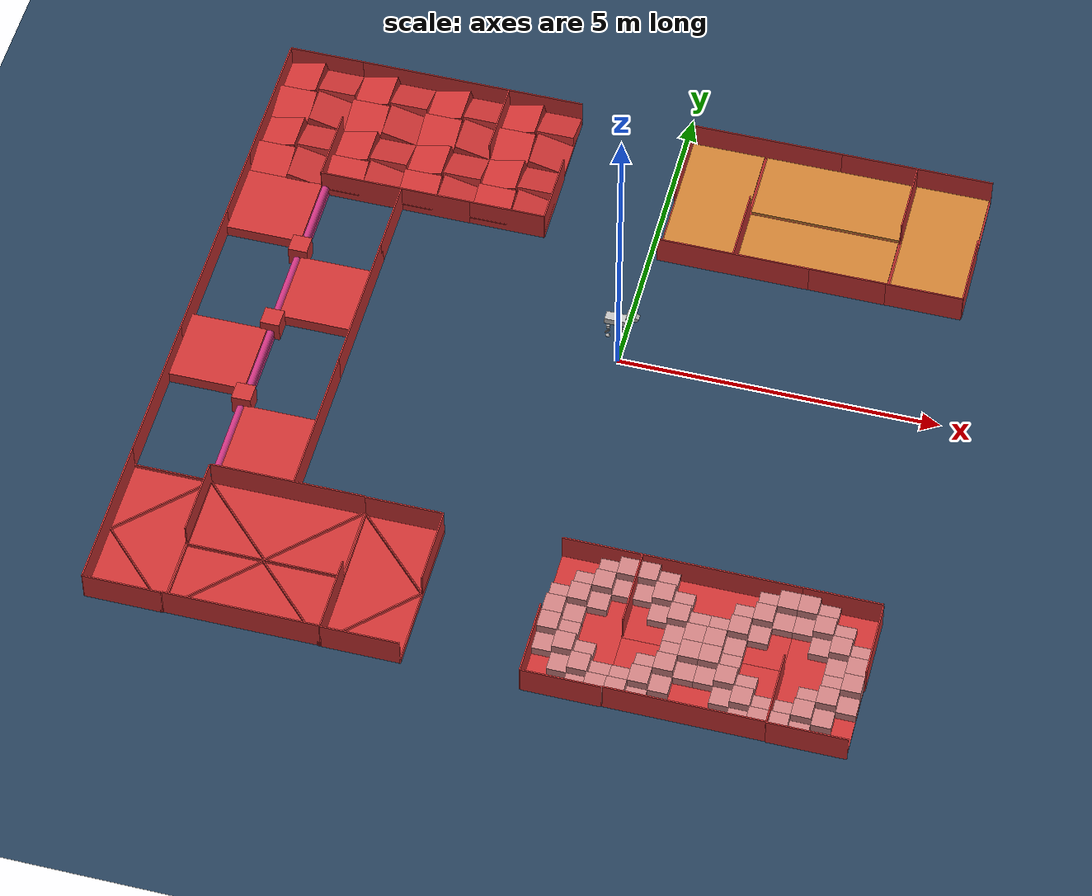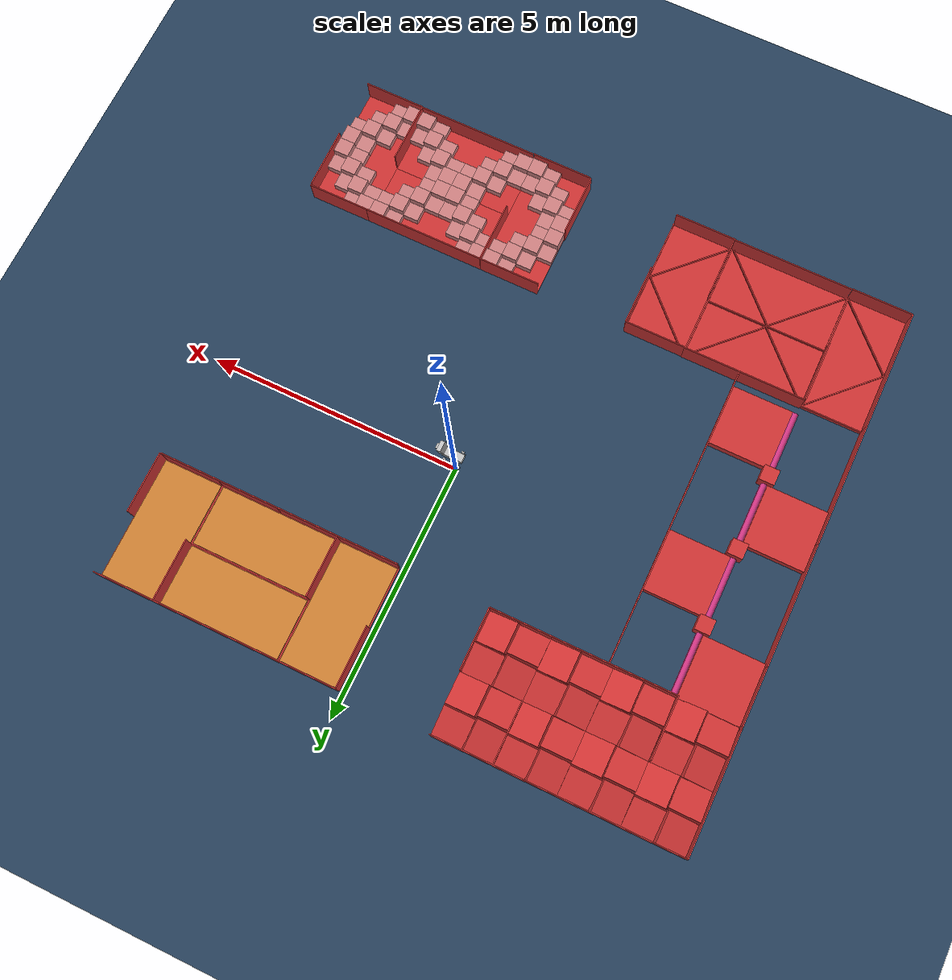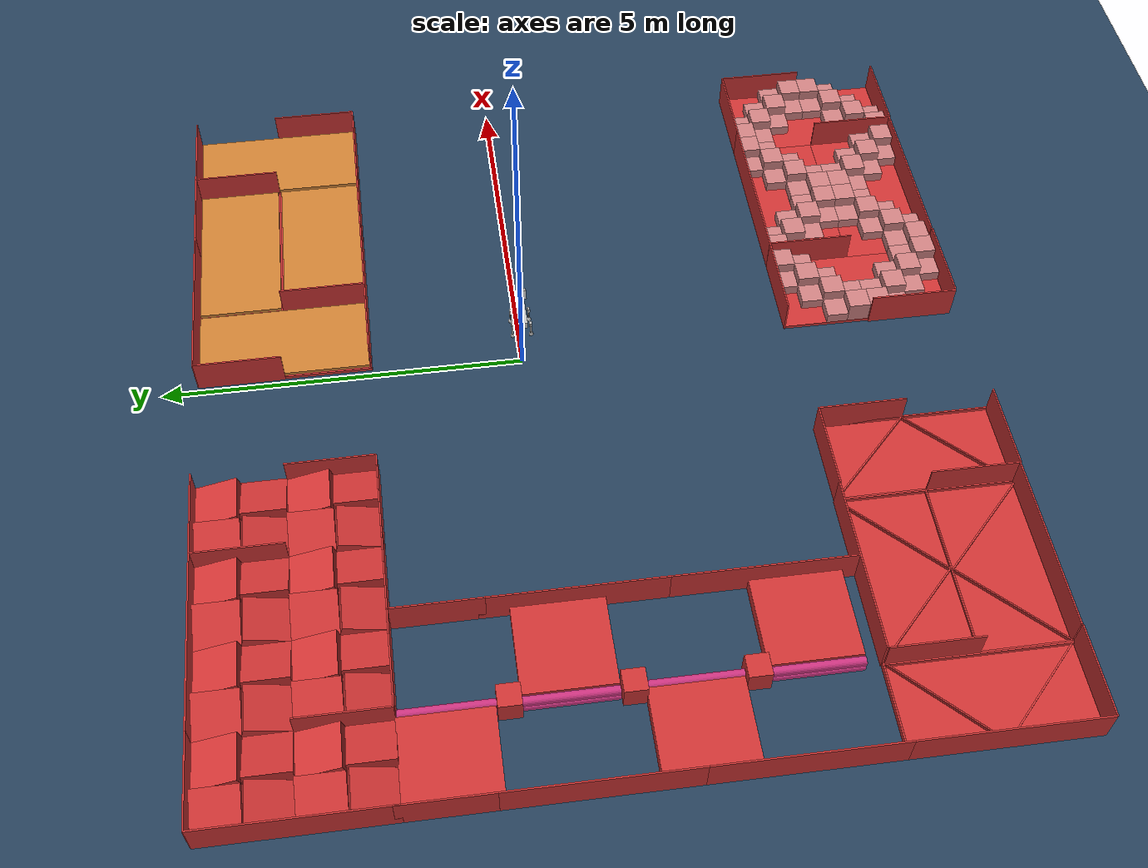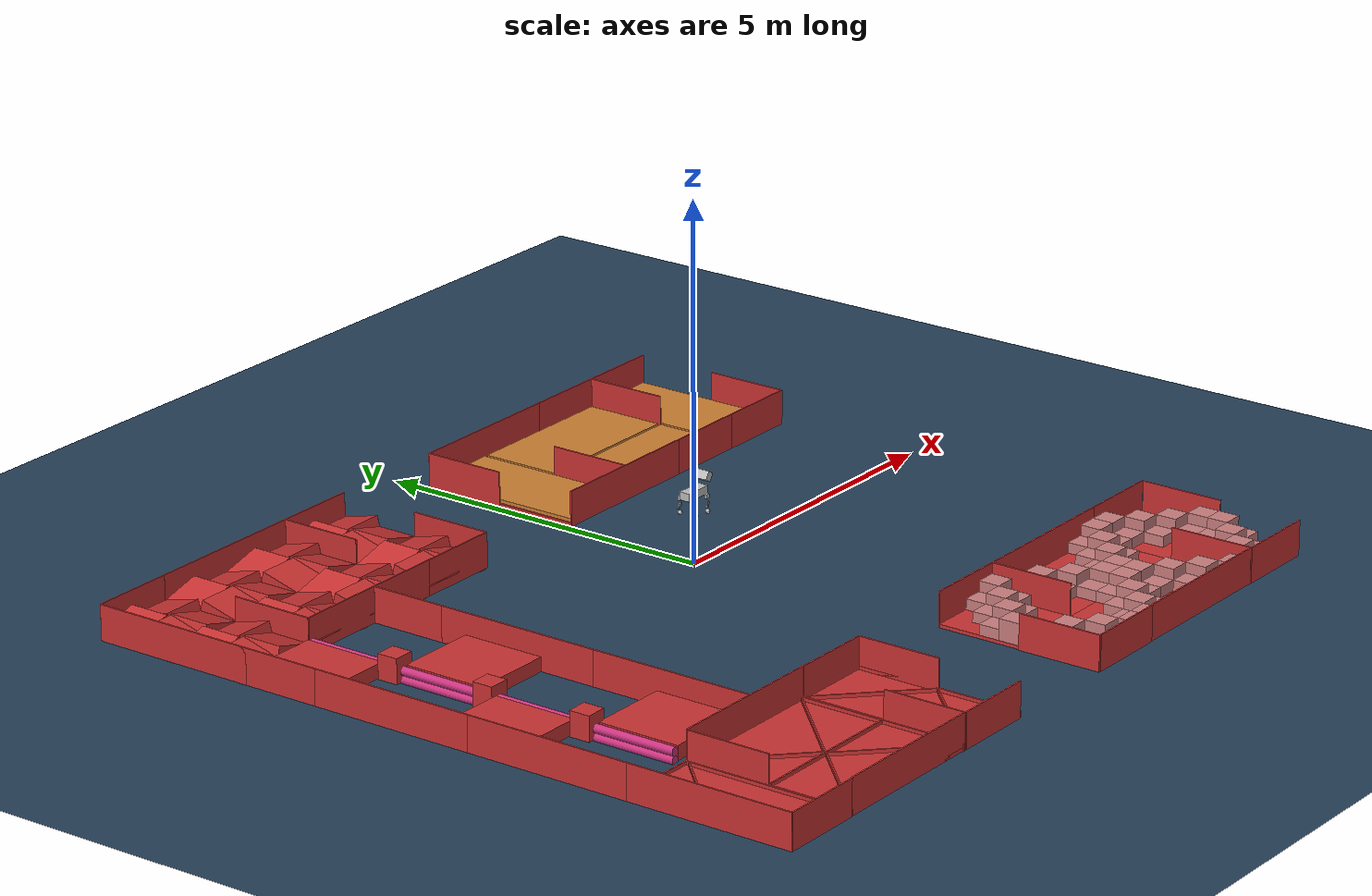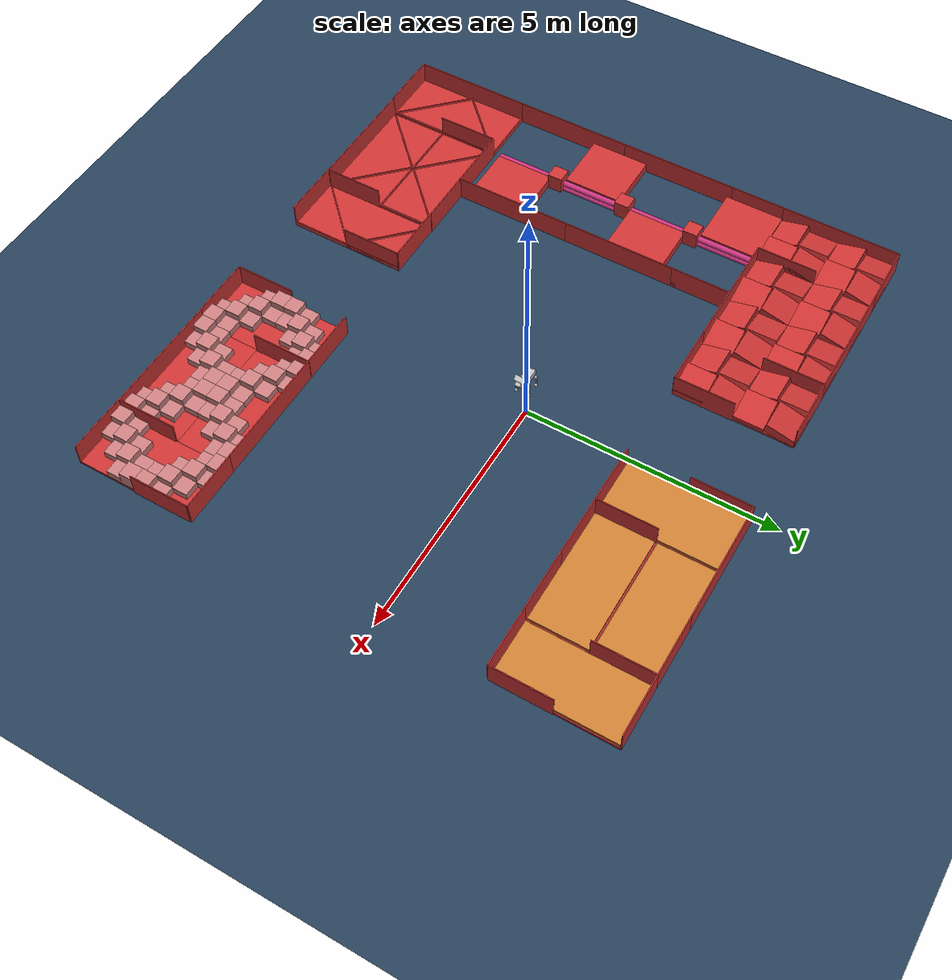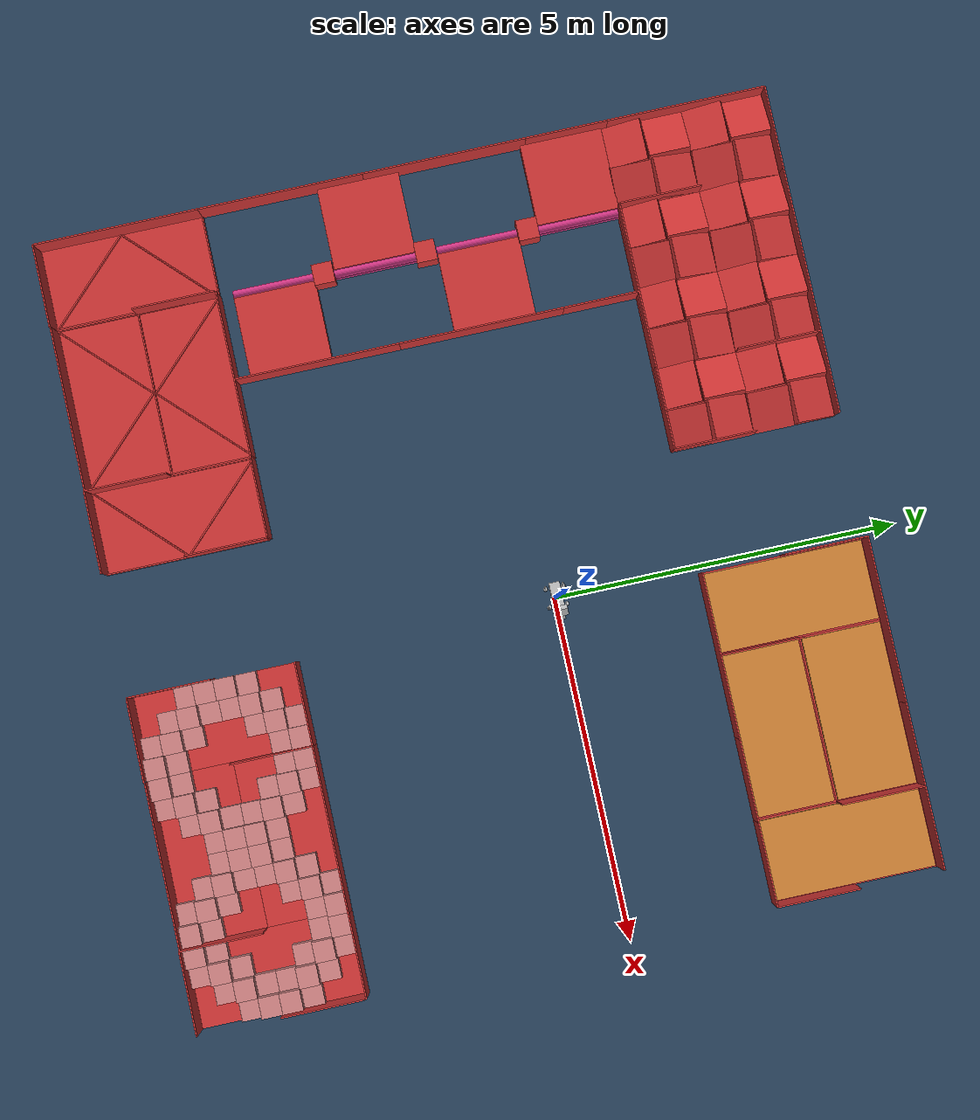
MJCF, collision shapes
<mujoco model="XXG scene">
  <include file="xxg.xml" />

  <statistic center="0 0 0.1" extent="0.8" />

  <visual>
    <headlight diffuse="0.6 0.6 0.6" ambient="0.3 0.3 0.3" specular="0 0 0" />
    <rgba haze="0.15 0.25 0.35 1" />
    <global azimuth="-130" elevation="-20" />
    <map znear="0.01" zfar="100"/>
  </visual>

  <asset>
    <texture type="skybox" builtin="gradient" rgb1="0.3 0.5 0.7" rgb2="0 0 0" width="512" height="3072" />
    <texture type="2d" name="groundplane" builtin="checker" mark="edge" rgb1="0.2 0.3 0.4" rgb2="0.1 0.2 0.3" markrgb="0.8 0.8 0.8" width="300" height="300" />
    <material name="groundplane" texture="groundplane" texuniform="true" texrepeat="5 5" reflectance="0.2" />
  <hfield name="perlin_hfield" size="1.0 0.75 0.2 0.2" file="../height_field.png" /><hfield name="image_hfield" size="1.0 1.0 0.02 0.1" file="../unitree_hfield.png" /></asset>

  <worldbody>
    <light pos="0 0 1.5" dir="0 0 -1" directional="true" />
    <geom name="floor" pos="0 0.0 0.001" size="0 0 0.05" type="plane" material="groundplane" />
    <geom name="phs_Cube" type="box" size="0.15 0.15 0.075" pos="4.75 -4.55 0.125" quat="1.0 0.0 0.0 0.0" rgba="0.8 0.5 0.5 1" solref="0.02 1" solimp="0.8 0.05 0.1"/>
    <geom name="phs_Cube2" type="box" size="1.2 0.6 0.025" pos="4.3 -5.0 0.025" quat="0.707107 0.0 0.0 -0.707107" rgba="0.8 0.2 0.2 1" solref="0.02 1" solimp="0.8 0.05 0.1" friction="0.8 0.2 0.05"/>
    <geom name="phs_Cube3" type="box" size="1.2 0.6 0.025" pos="2.5 -4.4 0.025" quat="0.0 0.0 0.0 -1.0" rgba="0.8 0.2 0.2 1" solref="0.02 1" solimp="0.8 0.05 0.1" friction="0.8 0.2 0.05"/>
    <geom name="phs_Cube4" type="box" size="1.2 0.6 0.025" pos="2.5 -5.6 0.025" quat="0.0 0.0 0.0 -1.0" rgba="0.8 0.2 0.2 1" solref="0.02 1" solimp="0.8 0.05 0.1" friction="0.8 0.2 0.05"/>
    <geom name="phs_Cube5" type="box" size="1.2 0.6 0.025" pos="0.7 -5.0 0.025" quat="0.707107 0.0 0.0 -0.707107" rgba="0.8 0.2 0.2 1" solref="0.02 1" solimp="0.8 0.05 0.1" friction="0.8 0.2 0.05"/>
    <geom name="phs_Cube6" type="box" size="1.2 0.6 0.025" pos="-2.3 -5.0 0.025" quat="0.707107 0.0 0.0 -0.707107" rgba="0.8 0.2 0.2 1" solref="0.02 1" solimp="0.8 0.05 0.1" friction="0.8 0.2 0.05"/>
    <geom name="phs_Cube7" type="box" size="1.2 0.6 0.025" pos="-4.1 -4.4 0.025" quat="0.0 0.0 0.0 -1.0" rgba="0.8 0.2 0.2 1" solref="0.02 1" solimp="0.8 0.05 0.1" friction="0.8 0.2 0.05"/>
    <geom name="phs_Cube8" type="box" size="1.2 0.6 0.025" pos="-4.1 -5.6 0.025" quat="0.0 0.0 0.0 -1.0" rgba="0.8 0.2 0.2 1" solref="0.02 1" solimp="0.8 0.05 0.1" friction="0.8 0.2 0.05"/>
    <geom name="phs_Cube9" type="box" size="1.2 0.6 0.025" pos="-5.9 -5.0 0.025" quat="0.707107 0.0 0.0 -0.707107" rgba="0.8 0.2 0.2 1" solref="0.02 1" solimp="0.8 0.05 0.1" friction="0.8 0.2 0.05"/>
    <geom name="phs_Cube10" type="box" size="1.2 0.6 0.025" pos="-2.3 3.3 0.025" quat="0.707107 0.0 0.0 -0.707107" rgba="0.8 0.2 0.2 1" solref="0.02 1" solimp="0.8 0.05 0.1" friction="0.8 0.2 0.05"/>
    <geom name="phs_Cube11" type="box" size="1.2 0.6 0.025" pos="-4.1 3.9 0.025" quat="0.0 0.0 0.0 -1.0" rgba="0.8 0.2 0.2 1" solref="0.02 1" solimp="0.8 0.05 0.1" friction="0.8 0.2 0.05"/>
    <geom name="phs_Cube12" type="box" size="1.2 0.6 0.025" pos="-4.1 2.7 0.025" quat="0.0 0.0 0.0 -1.0" rgba="0.8 0.2 0.2 1" solref="0.02 1" solimp="0.8 0.05 0.1" friction="0.8 0.2 0.05"/>
    <geom name="phs_Cube13" type="box" size="1.2 0.6 0.025" pos="-5.9 3.3 0.025" quat="0.707107 0.0 0.0 -0.707107" rgba="0.8 0.2 0.2 1" solref="0.02 1" solimp="0.8 0.05 0.1" friction="0.8 0.2 0.05"/>
    <geom name="phs_Cube14" type="box" size="1.2 0.6 0.025" pos="4.3 3.3 0.025" quat="0.707107 0.0 0.0 -0.707107" rgba="0.8 0.2 0.2 1" solref="0.02 1" solimp="0.8 0.05 0.1" friction="0.8 0.2 0.05"/>
    <geom name="phs_Cube15" type="box" size="1.2 0.6 0.025" pos="2.5 3.9 0.025" quat="0.0 0.0 0.0 -1.0" rgba="0.8 0.2 0.2 1" solref="0.02 1" solimp="0.8 0.05 0.1" friction="0.8 0.2 0.05"/>
    <geom name="phs_Cube16" type="box" size="1.2 0.6 0.025" pos="2.5 2.7 0.025" quat="0.0 0.0 0.0 -1.0" rgba="0.8 0.2 0.2 1" solref="0.02 1" solimp="0.8 0.05 0.1" friction="0.8 0.2 0.05"/>
    <geom name="phs_Cube17" type="box" size="1.2 0.6 0.025" pos="0.7 3.3 0.025" quat="0.707107 0.0 0.0 -0.707107" rgba="0.8 0.2 0.2 1" solref="0.02 1" solimp="0.8 0.05 0.1" friction="0.8 0.2 0.05"/>
    <geom name="phs_Cube18" type="box" size="0.15 0.15 0.15" pos="4.75 -4.85 0.2" quat="1.0 0.0 0.0 0.0" rgba="0.8 0.5 0.5 1" solref="0.02 1" solimp="0.8 0.05 0.1" friction="0.8 0.2 0.05"/>
    <geom name="phs_Cube19" type="box" size="0.15 0.15 0.15" pos="4.75 -5.15 0.2" quat="1.0 0.0 0.0 0.0" rgba="0.8 0.5 0.5 1" solref="0.02 1" solimp="0.8 0.05 0.1" friction="0.8 0.2 0.05"/>
    <geom name="phs_Cube20" type="box" size="0.15 0.15 0.15" pos="4.45 -5.45 0.2" quat="1.0 0.0 0.0 0.0" rgba="0.8 0.5 0.5 1" solref="0.02 1" solimp="0.8 0.05 0.1" friction="0.8 0.2 0.05"/>
    <geom name="phs_Cube21" type="box" size="0.15 0.15 0.15" pos="4.15 -5.75 0.2" quat="1.0 0.0 0.0 0.0" rgba="0.8 0.5 0.5 1" solref="0.02 1" solimp="0.8 0.05 0.1" friction="0.8 0.2 0.05"/>
    <geom name="phs_Cube22" type="box" size="0.15 0.15 0.15" pos="3.85 -6.05 0.2" quat="1.0 0.0 0.0 0.0" rgba="0.8 0.5 0.5 1" solref="0.02 1" solimp="0.8 0.05 0.1" friction="0.8 0.2 0.05"/>
    <geom name="phs_Cube23" type="box" size="0.15 0.15 0.15" pos="3.85 -3.95 0.2" quat="1.0 0.0 0.0 0.0" rgba="0.8 0.5 0.5 1" solref="0.02 1" solimp="0.8 0.05 0.1" friction="0.8 0.2 0.05"/>
    <geom name="phs_Cube24" type="box" size="0.15 0.15 0.15" pos="4.15 -4.25 0.2" quat="1.0 0.0 0.0 0.0" rgba="0.8 0.5 0.5 1" solref="0.02 1" solimp="0.8 0.05 0.1" friction="0.8 0.2 0.05"/>
    <geom name="phs_Cube25" type="box" size="0.15 0.15 0.15" pos="4.45 -4.55 0.2" quat="1.0 0.0 0.0 0.0" rgba="0.8 0.5 0.5 1" solref="0.02 1" solimp="0.8 0.05 0.1" friction="0.8 0.2 0.05"/>
    <geom name="phs_Cube26" type="box" size="0.15 0.15 0.075" pos="4.45 -4.25 0.125" quat="1.0 0.0 0.0 0.0" rgba="0.8 0.5 0.5 1" solref="0.02 1" solimp="0.8 0.05 0.1" friction="0.8 0.2 0.05"/>
    <geom name="phs_Cube27" type="box" size="0.15 0.15 0.075" pos="4.15 -3.95 0.125" quat="1.0 0.0 0.0 0.0" rgba="0.8 0.5 0.5 1" solref="0.02 1" solimp="0.8 0.05 0.1" friction="0.8 0.2 0.05"/>
    <geom name="phs_Cube28" type="box" size="0.15 0.15 0.075" pos="4.15 -4.55 0.125" quat="1.0 0.0 0.0 0.0" rgba="0.8 0.5 0.5 1" solref="0.02 1" solimp="0.8 0.05 0.1" friction="0.8 0.2 0.05"/>
    <geom name="phs_Cube29" type="box" size="0.15 0.15 0.075" pos="3.85 -4.25 0.125" quat="1.0 0.0 0.0 0.0" rgba="0.8 0.5 0.5 1" solref="0.02 1" solimp="0.8 0.05 0.1" friction="0.8 0.2 0.05"/>
    <geom name="phs_Cube30" type="box" size="0.15 0.15 0.075" pos="4.45 -4.85 0.125" quat="1.0 0.0 0.0 0.0" rgba="0.8 0.5 0.5 1" solref="0.02 1" solimp="0.8 0.05 0.1" friction="0.8 0.2 0.05"/>
    <geom name="phs_Cube31" type="box" size="0.15 0.15 0.075" pos="4.45 -5.15 0.125" quat="1.0 0.0 0.0 0.0" rgba="0.8 0.5 0.5 1" solref="0.02 1" solimp="0.8 0.05 0.1" friction="0.8 0.2 0.05"/>
    <geom name="phs_Cube32" type="box" size="0.15 0.15 0.075" pos="4.45 -5.75 0.125" quat="1.0 0.0 0.0 0.0" rgba="0.8 0.5 0.5 1" solref="0.02 1" solimp="0.8 0.05 0.1" friction="0.8 0.2 0.05"/>
    <geom name="phs_Cube33" type="box" size="0.15 0.15 0.075" pos="4.75 -5.45 0.125" quat="1.0 0.0 0.0 0.0" rgba="0.8 0.5 0.5 1" solref="0.02 1" solimp="0.8 0.05 0.1" friction="0.8 0.2 0.05"/>
    <geom name="phs_Cube34" type="box" size="0.15 0.15 0.075" pos="4.15 -5.45 0.125" quat="1.0 0.0 0.0 0.0" rgba="0.8 0.5 0.5 1" solref="0.02 1" solimp="0.8 0.05 0.1" friction="0.8 0.2 0.05"/>
    <geom name="phs_Cube35" type="box" size="0.15 0.15 0.075" pos="4.15 -6.05 0.125" quat="1.0 0.0 0.0 0.0" rgba="0.8 0.5 0.5 1" solref="0.02 1" solimp="0.8 0.05 0.1" friction="0.8 0.2 0.05"/>
    <geom name="phs_Cube36" type="box" size="0.15 0.15 0.075" pos="3.85 -5.75 0.125" quat="1.0 0.0 0.0 0.0" rgba="0.8 0.5 0.5 1" solref="0.02 1" solimp="0.8 0.05 0.1" friction="0.8 0.2 0.05"/>
    <geom name="phs_Cube37" type="box" size="0.15 0.15 0.075" pos="0.25 -5.45 0.125" quat="0.0 0.0 0.0 -1.0" rgba="0.8 0.5 0.5 1" solref="0.02 1" solimp="0.8 0.05 0.1" friction="0.8 0.2 0.05"/>
    <geom name="phs_Cube38" type="box" size="0.15 0.15 0.15" pos="0.25 -5.15 0.2" quat="0.0 0.0 0.0 -1.0" rgba="0.8 0.5 0.5 1" solref="0.02 1" solimp="0.8 0.05 0.1" friction="0.8 0.2 0.05"/>
    <geom name="phs_Cube39" type="box" size="0.15 0.15 0.15" pos="0.25 -4.85 0.2" quat="0.0 0.0 0.0 -1.0" rgba="0.8 0.5 0.5 1" solref="0.02 1" solimp="0.8 0.05 0.1" friction="0.8 0.2 0.05"/>
    <geom name="phs_Cube40" type="box" size="0.15 0.15 0.15" pos="0.55 -4.55 0.2" quat="0.0 0.0 0.0 -1.0" rgba="0.8 0.5 0.5 1" solref="0.02 1" solimp="0.8 0.05 0.1" friction="0.8 0.2 0.05"/>
    <geom name="phs_Cube41" type="box" size="0.15 0.15 0.15" pos="0.85 -4.25 0.2" quat="0.0 0.0 0.0 -1.0" rgba="0.8 0.5 0.5 1" solref="0.02 1" solimp="0.8 0.05 0.1" friction="0.8 0.2 0.05"/>
    <geom name="phs_Cube42" type="box" size="0.15 0.15 0.15" pos="1.15 -3.95 0.2" quat="0.0 0.0 0.0 -1.0" rgba="0.8 0.5 0.5 1" solref="0.02 1" solimp="0.8 0.05 0.1" friction="0.8 0.2 0.05"/>
    <geom name="phs_Cube43" type="box" size="0.15 0.15 0.15" pos="1.15 -6.05 0.2" quat="0.0 0.0 0.0 -1.0" rgba="0.8 0.5 0.5 1" solref="0.02 1" solimp="0.8 0.05 0.1" friction="0.8 0.2 0.05"/>
    <geom name="phs_Cube44" type="box" size="0.15 0.15 0.15" pos="0.85 -5.75 0.2" quat="0.0 0.0 0.0 -1.0" rgba="0.8 0.5 0.5 1" solref="0.02 1" solimp="0.8 0.05 0.1" friction="0.8 0.2 0.05"/>
    <geom name="phs_Cube45" type="box" size="0.15 0.15 0.15" pos="0.55 -5.45 0.2" quat="0.0 0.0 0.0 -1.0" rgba="0.8 0.5 0.5 1" solref="0.02 1" solimp="0.8 0.05 0.1" friction="0.8 0.2 0.05"/>
    <geom name="phs_Cube46" type="box" size="0.15 0.15 0.075" pos="0.55 -5.75 0.125" quat="0.0 0.0 0.0 -1.0" rgba="0.8 0.5 0.5 1" solref="0.02 1" solimp="0.8 0.05 0.1" friction="0.8 0.2 0.05"/>
    <geom name="phs_Cube47" type="box" size="0.15 0.15 0.075" pos="0.85 -6.05 0.125" quat="0.0 0.0 0.0 -1.0" rgba="0.8 0.5 0.5 1" solref="0.02 1" solimp="0.8 0.05 0.1" friction="0.8 0.2 0.05"/>
    <geom name="phs_Cube48" type="box" size="0.15 0.15 0.075" pos="0.85 -5.45 0.125" quat="0.0 0.0 0.0 -1.0" rgba="0.8 0.5 0.5 1" solref="0.02 1" solimp="0.8 0.05 0.1" friction="0.8 0.2 0.05"/>
    <geom name="phs_Cube49" type="box" size="0.15 0.15 0.075" pos="1.15 -5.75 0.125" quat="0.0 0.0 0.0 -1.0" rgba="0.8 0.5 0.5 1" solref="0.02 1" solimp="0.8 0.05 0.1" friction="0.8 0.2 0.05"/>
    <geom name="phs_Cube50" type="box" size="0.15 0.15 0.075" pos="0.55 -5.15 0.125" quat="0.0 0.0 0.0 -1.0" rgba="0.8 0.5 0.5 1" solref="0.02 1" solimp="0.8 0.05 0.1" friction="0.8 0.2 0.05"/>
    <geom name="phs_Cube51" type="box" size="0.15 0.15 0.075" pos="0.55 -4.85 0.125" quat="0.0 0.0 0.0 -1.0" rgba="0.8 0.5 0.5 1" solref="0.02 1" solimp="0.8 0.05 0.1" friction="0.8 0.2 0.05"/>
    <geom name="phs_Cube52" type="box" size="0.15 0.15 0.075" pos="0.55 -4.25 0.125" quat="0.0 0.0 0.0 -1.0" rgba="0.8 0.5 0.5 1" solref="0.02 1" solimp="0.8 0.05 0.1" friction="0.8 0.2 0.05"/>
    <geom name="phs_Cube53" type="box" size="0.15 0.15 0.075" pos="0.25 -4.55 0.125" quat="0.0 0.0 0.0 -1.0" rgba="0.8 0.5 0.5 1" solref="0.02 1" solimp="0.8 0.05 0.1" friction="0.8 0.2 0.05"/>
    <geom name="phs_Cube54" type="box" size="0.15 0.15 0.075" pos="0.85 -4.55 0.125" quat="0.0 0.0 0.0 -1.0" rgba="0.8 0.5 0.5 1" solref="0.02 1" solimp="0.8 0.05 0.1" friction="0.8 0.2 0.05"/>
    <geom name="phs_Cube55" type="box" size="0.15 0.15 0.075" pos="0.85 -3.95 0.125" quat="0.0 0.0 0.0 -1.0" rgba="0.8 0.5 0.5 1" solref="0.02 1" solimp="0.8 0.05 0.1" friction="0.8 0.2 0.05"/>
    <geom name="phs_Cube56" type="box" size="0.15 0.15 0.075" pos="1.15 -4.25 0.125" quat="0.0 0.0 0.0 -1.0" rgba="0.8 0.5 0.5 1" solref="0.02 1" solimp="0.8 0.05 0.1" friction="0.8 0.2 0.05"/>
    <geom name="phs_Cube57" type="box" size="0.15 0.15 0.075" pos="2.95 -4.85 0.125" quat="0.707107 0.0 0.0 -0.707107" rgba="0.8 0.5 0.5 1" solref="0.02 1" solimp="0.8 0.05 0.1" friction="0.8 0.2 0.05"/>
    <geom name="phs_Cube58" type="box" size="0.15 0.15 0.15" pos="2.65 -4.85 0.2" quat="0.707107 0.0 0.0 -0.707107" rgba="0.8 0.5 0.5 1" solref="0.02 1" solimp="0.8 0.05 0.1" friction="0.8 0.2 0.05"/>
    <geom name="phs_Cube59" type="box" size="0.15 0.15 0.15" pos="2.35 -4.85 0.2" quat="0.707107 0.0 0.0 -0.707107" rgba="0.8 0.5 0.5 1" solref="0.02 1" solimp="0.8 0.05 0.1" friction="0.8 0.2 0.05"/>
    <geom name="phs_Cube60" type="box" size="0.15 0.15 0.15" pos="2.05 -4.55 0.2" quat="0.707107 0.0 0.0 -0.707107" rgba="0.8 0.5 0.5 1" solref="0.02 1" solimp="0.8 0.05 0.1" friction="0.8 0.2 0.05"/>
    <geom name="phs_Cube61" type="box" size="0.15 0.15 0.15" pos="1.75 -4.25 0.2" quat="0.707107 0.0 0.0 -0.707107" rgba="0.8 0.5 0.5 1" solref="0.02 1" solimp="0.8 0.05 0.1" friction="0.8 0.2 0.05"/>
    <geom name="phs_Cube62" type="box" size="0.15 0.15 0.15" pos="1.45 -3.95 0.2" quat="0.707107 0.0 0.0 -0.707107" rgba="0.8 0.5 0.5 1" solref="0.02 1" solimp="0.8 0.05 0.1" friction="0.8 0.2 0.05"/>
    <geom name="phs_Cube63" type="box" size="0.15 0.15 0.15" pos="3.55 -3.95 0.2" quat="0.707107 0.0 0.0 -0.707107" rgba="0.8 0.5 0.5 1" solref="0.02 1" solimp="0.8 0.05 0.1" friction="0.8 0.2 0.05"/>
    <geom name="phs_Cube64" type="box" size="0.15 0.15 0.15" pos="3.25 -4.25 0.2" quat="0.707107 0.0 0.0 -0.707107" rgba="0.8 0.5 0.5 1" solref="0.02 1" solimp="0.8 0.05 0.1" friction="0.8 0.2 0.05"/>
    <geom name="phs_Cube65" type="box" size="0.15 0.15 0.15" pos="2.95 -4.55 0.2" quat="0.707107 0.0 0.0 -0.707107" rgba="0.8 0.5 0.5 1" solref="0.02 1" solimp="0.8 0.05 0.1" friction="0.8 0.2 0.05"/>
    <geom name="phs_Cube66" type="box" size="0.15 0.15 0.075" pos="3.25 -4.55 0.125" quat="0.707107 0.0 0.0 -0.707107" rgba="0.8 0.5 0.5 1" solref="0.02 1" solimp="0.8 0.05 0.1" friction="0.8 0.2 0.05"/>
    <geom name="phs_Cube67" type="box" size="0.15 0.15 0.075" pos="3.55 -4.25 0.125" quat="0.707107 0.0 0.0 -0.707107" rgba="0.8 0.5 0.5 1" solref="0.02 1" solimp="0.8 0.05 0.1" friction="0.8 0.2 0.05"/>
    <geom name="phs_Cube68" type="box" size="0.15 0.15 0.075" pos="2.95 -4.25 0.125" quat="0.707107 0.0 0.0 -0.707107" rgba="0.8 0.5 0.5 1" solref="0.02 1" solimp="0.8 0.05 0.1" friction="0.8 0.2 0.05"/>
    <geom name="phs_Cube69" type="box" size="0.15 0.15 0.075" pos="3.25 -3.95 0.125" quat="0.707107 0.0 0.0 -0.707107" rgba="0.8 0.5 0.5 1" solref="0.02 1" solimp="0.8 0.05 0.1" friction="0.8 0.2 0.05"/>
    <geom name="phs_Cube70" type="box" size="0.15 0.15 0.075" pos="2.65 -4.55 0.125" quat="0.707107 0.0 0.0 -0.707107" rgba="0.8 0.5 0.5 1" solref="0.02 1" solimp="0.8 0.05 0.1" friction="0.8 0.2 0.05"/>
    <geom name="phs_Cube71" type="box" size="0.15 0.15 0.075" pos="2.35 -4.55 0.125" quat="0.707107 0.0 0.0 -0.707107" rgba="0.8 0.5 0.5 1" solref="0.02 1" solimp="0.8 0.05 0.1" friction="0.8 0.2 0.05"/>
    <geom name="phs_Cube72" type="box" size="0.15 0.15 0.075" pos="1.75 -4.55 0.125" quat="0.707107 0.0 0.0 -0.707107" rgba="0.8 0.5 0.5 1" solref="0.02 1" solimp="0.8 0.05 0.1" friction="0.8 0.2 0.05"/>
    <geom name="phs_Cube73" type="box" size="0.15 0.15 0.075" pos="2.05 -4.85 0.125" quat="0.707107 0.0 0.0 -0.707107" rgba="0.8 0.5 0.5 1" solref="0.02 1" solimp="0.8 0.05 0.1" friction="0.8 0.2 0.05"/>
    <geom name="phs_Cube74" type="box" size="0.15 0.15 0.075" pos="2.05 -4.25 0.125" quat="0.707107 0.0 0.0 -0.707107" rgba="0.8 0.5 0.5 1" solref="0.02 1" solimp="0.8 0.05 0.1" friction="0.8 0.2 0.05"/>
    <geom name="phs_Cube75" type="box" size="0.15 0.15 0.075" pos="1.45 -4.25 0.125" quat="0.707107 0.0 0.0 -0.707107" rgba="0.8 0.5 0.5 1" solref="0.02 1" solimp="0.8 0.05 0.1" friction="0.8 0.2 0.05"/>
    <geom name="phs_Cube76" type="box" size="0.15 0.15 0.075" pos="1.75 -3.95 0.125" quat="0.707107 0.0 0.0 -0.707107" rgba="0.8 0.5 0.5 1" solref="0.02 1" solimp="0.8 0.05 0.1" friction="0.8 0.2 0.05"/>
    <geom name="phs_Cube77" type="box" size="0.15 0.15 0.075" pos="2.05 -5.15 0.125" quat="0.707107 0.0 0.0 0.707107" rgba="0.8 0.5 0.5 1" solref="0.02 1" solimp="0.8 0.05 0.1" friction="0.8 0.2 0.05"/>
    <geom name="phs_Cube78" type="box" size="0.15 0.15 0.15" pos="2.35 -5.15 0.2" quat="0.707107 0.0 0.0 0.707107" rgba="0.8 0.5 0.5 1" solref="0.02 1" solimp="0.8 0.05 0.1" friction="0.8 0.2 0.05"/>
    <geom name="phs_Cube79" type="box" size="0.15 0.15 0.15" pos="2.65 -5.15 0.2" quat="0.707107 0.0 0.0 0.707107" rgba="0.8 0.5 0.5 1" solref="0.02 1" solimp="0.8 0.05 0.1" friction="0.8 0.2 0.05"/>
    <geom name="phs_Cube80" type="box" size="0.15 0.15 0.15" pos="2.95 -5.45 0.2" quat="0.707107 0.0 0.0 0.707107" rgba="0.8 0.5 0.5 1" solref="0.02 1" solimp="0.8 0.05 0.1" friction="0.8 0.2 0.05"/>
    <geom name="phs_Cube81" type="box" size="0.15 0.15 0.15" pos="3.25 -5.75 0.2" quat="0.707107 0.0 0.0 0.707107" rgba="0.8 0.5 0.5 1" solref="0.02 1" solimp="0.8 0.05 0.1" friction="0.8 0.2 0.05"/>
    <geom name="phs_Cube82" type="box" size="0.15 0.15 0.15" pos="3.55 -6.05 0.2" quat="0.707107 0.0 0.0 0.707107" rgba="0.8 0.5 0.5 1" solref="0.02 1" solimp="0.8 0.05 0.1" friction="0.8 0.2 0.05"/>
    <geom name="phs_Cube83" type="box" size="0.15 0.15 0.15" pos="1.45 -6.05 0.2" quat="0.707107 0.0 0.0 0.707107" rgba="0.8 0.5 0.5 1" solref="0.02 1" solimp="0.8 0.05 0.1" friction="0.8 0.2 0.05"/>
    <geom name="phs_Cube84" type="box" size="0.15 0.15 0.15" pos="1.75 -5.75 0.2" quat="0.707107 0.0 0.0 0.707107" rgba="0.8 0.5 0.5 1" solref="0.02 1" solimp="0.8 0.05 0.1" friction="0.8 0.2 0.05"/>
    <geom name="phs_Cube85" type="box" size="0.15 0.15 0.15" pos="2.05 -5.45 0.2" quat="0.707107 0.0 0.0 0.707107" rgba="0.8 0.5 0.5 1" solref="0.02 1" solimp="0.8 0.05 0.1" friction="0.8 0.2 0.05"/>
    <geom name="phs_Cube86" type="box" size="0.15 0.15 0.075" pos="1.75 -5.45 0.125" quat="0.707107 0.0 0.0 0.707107" rgba="0.8 0.5 0.5 1" solref="0.02 1" solimp="0.8 0.05 0.1" friction="0.8 0.2 0.05"/>
    <geom name="phs_Cube87" type="box" size="0.15 0.15 0.075" pos="1.45 -5.75 0.125" quat="0.707107 0.0 0.0 0.707107" rgba="0.8 0.5 0.5 1" solref="0.02 1" solimp="0.8 0.05 0.1" friction="0.8 0.2 0.05"/>
    <geom name="phs_Cube88" type="box" size="0.15 0.15 0.075" pos="2.05 -5.75 0.125" quat="0.707107 0.0 0.0 0.707107" rgba="0.8 0.5 0.5 1" solref="0.02 1" solimp="0.8 0.05 0.1" friction="0.8 0.2 0.05"/>
    <geom name="phs_Cube89" type="box" size="0.15 0.15 0.075" pos="1.75 -6.05 0.125" quat="0.707107 0.0 0.0 0.707107" rgba="0.8 0.5 0.5 1" solref="0.02 1" solimp="0.8 0.05 0.1" friction="0.8 0.2 0.05"/>
    <geom name="phs_Cube90" type="box" size="0.15 0.15 0.075" pos="2.35 -5.45 0.125" quat="0.707107 0.0 0.0 0.707107" rgba="0.8 0.5 0.5 1" solref="0.02 1" solimp="0.8 0.05 0.1" friction="0.8 0.2 0.05"/>
    <geom name="phs_Cube91" type="box" size="0.15 0.15 0.075" pos="2.65 -5.45 0.125" quat="0.707107 0.0 0.0 0.707107" rgba="0.8 0.5 0.5 1" solref="0.02 1" solimp="0.8 0.05 0.1" friction="0.8 0.2 0.05"/>
    <geom name="phs_Cube92" type="box" size="0.15 0.15 0.075" pos="3.25 -5.45 0.125" quat="0.707107 0.0 0.0 0.707107" rgba="0.8 0.5 0.5 1" solref="0.02 1" solimp="0.8 0.05 0.1" friction="0.8 0.2 0.05"/>
    <geom name="phs_Cube93" type="box" size="0.15 0.15 0.075" pos="2.95 -5.15 0.125" quat="0.707107 0.0 0.0 0.707107" rgba="0.8 0.5 0.5 1" solref="0.02 1" solimp="0.8 0.05 0.1" friction="0.8 0.2 0.05"/>
    <geom name="phs_Cube94" type="box" size="0.15 0.15 0.075" pos="2.95 -5.75 0.125" quat="0.707107 0.0 0.0 0.707107" rgba="0.8 0.5 0.5 1" solref="0.02 1" solimp="0.8 0.05 0.1" friction="0.8 0.2 0.05"/>
    <geom name="phs_Cube95" type="box" size="0.15 0.15 0.075" pos="3.55 -5.75 0.125" quat="0.707107 0.0 0.0 0.707107" rgba="0.8 0.5 0.5 1" solref="0.02 1" solimp="0.8 0.05 0.1" friction="0.8 0.2 0.05"/>
    <geom name="phs_Cube96" type="box" size="0.15 0.15 0.075" pos="3.25 -6.05 0.125" quat="0.707107 0.0 0.0 0.707107" rgba="0.8 0.5 0.5 1" solref="0.02 1" solimp="0.8 0.05 0.1" friction="0.8 0.2 0.05"/>
    <geom name="phs_Cube97" type="box" size="0.6 0.01 0.25" pos="4.31 -6.21 0.25" quat="1.0 0.0 0.0 0.0" rgba="0.8 0.2 0.2 1" solref="0.02 1" solimp="0.8 0.05 0.1" friction="0.8 0.2 0.05"/>
    <geom name="phs_Cube98" type="box" size="0.6 0.01 0.25" pos="4.31 -3.79 0.25" quat="1.0 0.0 0.0 0.0" rgba="0.8 0.2 0.2 1" solref="0.02 1" solimp="0.8 0.05 0.1" friction="0.8 0.2 0.05"/>
    <geom name="phs_Cube99" type="box" size="0.6 0.01 0.25" pos="0.7 -6.21 0.25" quat="1.0 0.0 0.0 0.0" rgba="0.8 0.2 0.2 1" solref="0.02 1" solimp="0.8 0.05 0.1" friction="0.8 0.2 0.05"/>
    <geom name="phs_Cube100" type="box" size="0.6 0.01 0.25" pos="0.7 -3.79 0.25" quat="1.0 0.0 0.0 0.0" rgba="0.8 0.2 0.2 1" solref="0.02 1" solimp="0.8 0.05 0.1" friction="0.8 0.2 0.05"/>
    <geom name="phs_Cube101" type="box" size="0.6 0.01 0.25" pos="4.91 -4.41 0.25" quat="0.707107 0.0 0.0 -0.707107" rgba="0.8 0.2 0.2 1" solref="0.02 1" solimp="0.8 0.05 0.1" friction="0.8 0.2 0.05"/>
    <geom name="phs_Cube102" type="box" size="0.6 0.01 0.25" pos="1.31 -4.39 0.25" quat="0.707107 0.0 0.0 -0.707107" rgba="0.8 0.2 0.2 1" solref="0.02 1" solimp="0.8 0.05 0.1" friction="0.8 0.2 0.05"/>
    <geom name="phs_Cube103" type="box" size="0.6 0.01 0.25" pos="0.09 -5.61 0.25" quat="0.707107 0.0 0.0 -0.707107" rgba="0.8 0.2 0.2 1" solref="0.02 1" solimp="0.8 0.05 0.1" friction="0.8 0.2 0.05"/>
    <geom name="phs_Cube104" type="box" size="0.6 0.01 0.25" pos="3.71 -5.61 0.25" quat="0.707107 0.0 0.0 -0.707107" rgba="0.8 0.2 0.2 1" solref="0.02 1" solimp="0.8 0.05 0.1" friction="0.8 0.2 0.05"/>
    <geom name="phs_Cube105" type="box" size="1.2 0.01 0.25" pos="2.51 -3.79 0.25" quat="1.0 0.0 0.0 0.0" rgba="0.8 0.2 0.2 1" solref="0.02 1" solimp="0.8 0.05 0.1" friction="0.8 0.2 0.05"/>
    <geom name="phs_Cube106" type="box" size="1.2 0.01 0.25" pos="2.51 -6.2 0.25" quat="1.0 0.0 0.0 0.0" rgba="0.8 0.2 0.2 1" solref="0.02 1" solimp="0.8 0.05 0.1" friction="0.8 0.2 0.05"/>
    <geom name="phs_Cube107" type="box" size="1.2 0.01 0.25" pos="-4.09 -6.19 0.25" quat="1.0 0.0 0.0 0.0" rgba="0.8 0.2 0.2 1" solref="0.02 1" solimp="0.8 0.05 0.1" friction="0.8 0.2 0.05"/>
    <geom name="phs_Cube108" type="box" size="1.2 0.01 0.25" pos="-4.09 -3.79 0.25" quat="1.0 0.0 0.0 0.0" rgba="0.8 0.2 0.2 1" solref="0.02 1" solimp="0.8 0.05 0.1" friction="0.8 0.2 0.05"/>
    <geom name="phs_Cube109" type="box" size="1.2 0.01 0.25" pos="-6.5 -5.0 0.25" quat="0.707107 0.0 0.0 0.707107" rgba="0.8 0.2 0.2 1" solref="0.02 1" solimp="0.8 0.05 0.1" friction="0.8 0.2 0.05"/>
    <geom name="phs_Cube110" type="box" size="1.2 0.01 0.25" pos="-6.5 -2.6 0.25" quat="0.707107 0.0 0.0 0.707107" rgba="0.8 0.2 0.2 1" solref="0.02 1" solimp="0.8 0.05 0.1" friction="0.8 0.2 0.05"/>
    <geom name="phs_Cube111" type="box" size="1.2 0.01 0.25" pos="-6.5 -0.2 0.25" quat="0.707107 0.0 0.0 0.707107" rgba="0.8 0.2 0.2 1" solref="0.02 1" solimp="0.8 0.05 0.1" friction="0.8 0.2 0.05"/>
    <geom name="phs_Cube112" type="box" size="1.2 0.01 0.25" pos="-4.0 -2.6 0.25" quat="0.707107 0.0 0.0 0.707107" rgba="0.8 0.2 0.2 1" solref="0.02 1" solimp="0.8 0.05 0.1" friction="0.8 0.2 0.05"/>
    <geom name="phs_Cube113" type="box" size="1.2 0.01 0.25" pos="-4.0 -0.2 0.25" quat="0.707107 0.0 0.0 0.707107" rgba="0.8 0.2 0.2 1" solref="0.02 1" solimp="0.8 0.05 0.1" friction="0.8 0.2 0.05"/>
    <geom name="phs_Cube114" type="box" size="0.6 0.01 0.25" pos="-1.7 -4.41 0.25" quat="0.707107 0.0 0.0 -0.707107" rgba="0.8 0.2 0.2 1" solref="0.02 1" solimp="0.8 0.05 0.1" friction="0.8 0.2 0.05"/>
    <geom name="phs_Cube115" type="box" size="0.6 0.01 0.25" pos="-5.3 -4.41 0.25" quat="0.707107 0.0 0.0 -0.707107" rgba="0.8 0.2 0.2 1" solref="0.02 1" solimp="0.8 0.05 0.1" friction="0.8 0.2 0.05"/>
    <geom name="phs_Cube116" type="box" size="0.6 0.01 0.25" pos="-2.9 -5.61 0.25" quat="0.707107 0.0 0.0 -0.707107" rgba="0.8 0.2 0.2 1" solref="0.02 1" solimp="0.8 0.05 0.1" friction="0.8 0.2 0.05"/>
    <geom name="phs_Cube117" type="box" size="0.6 0.01 0.25" pos="-2.3 -6.2 0.25" quat="0.0 0.0 0.0 -1.0" rgba="0.8 0.2 0.2 1" solref="0.02 1" solimp="0.8 0.05 0.1" friction="0.8 0.2 0.05"/>
    <geom name="phs_Cube118" type="box" size="0.6 0.01 0.25" pos="-2.3 -3.8 0.25" quat="0.0 0.0 0.0 -1.0" rgba="0.8 0.2 0.2 1" solref="0.02 1" solimp="0.8 0.05 0.1" friction="0.8 0.2 0.05"/>
    <geom name="phs_Cube119" type="box" size="0.6 0.01 0.25" pos="-5.9 -6.2 0.25" quat="0.0 0.0 0.0 -1.0" rgba="0.8 0.2 0.2 1" solref="0.02 1" solimp="0.8 0.05 0.1" friction="0.8 0.2 0.05"/>
    <geom name="phs_Cube120" type="box" size="0.6 0.01 0.25" pos="-6.5 1.59 0.25" quat="0.707107 0.0 0.0 -0.707107" rgba="0.8 0.2 0.2 1" solref="0.02 1" solimp="0.8 0.05 0.1" friction="0.8 0.2 0.05"/>
    <geom name="phs_Cube121" type="box" size="0.6 0.01 0.25" pos="-4.0 1.5 0.25" quat="0.707107 0.0 0.0 -0.707107" rgba="0.8 0.2 0.2 1" solref="0.02 1" solimp="0.8 0.05 0.1" friction="0.8 0.2 0.05"/>
    <geom name="phs_Cube122" type="box" size="0.6 0.01 0.25" pos="-5.3 2.7 0.25" quat="0.707107 0.0 0.0 -0.707107" rgba="0.8 0.2 0.2 1" solref="0.02 1" solimp="0.8 0.05 0.1" friction="0.8 0.2 0.05"/>
    <geom name="phs_Cube123" type="box" size="0.6 0.01 0.25" pos="-1.7 2.7 0.25" quat="0.707107 0.0 0.0 -0.707107" rgba="0.8 0.2 0.2 1" solref="0.02 1" solimp="0.8 0.05 0.1" friction="0.8 0.2 0.05"/>
    <geom name="phs_Cube124" type="box" size="0.6 0.01 0.25" pos="-2.3 2.1 0.25" quat="0.0 0.0 0.0 -1.0" rgba="0.8 0.2 0.2 1" solref="0.02 1" solimp="0.8 0.05 0.1" friction="0.8 0.2 0.05"/>
    <geom name="phs_Cube125" type="box" size="0.6 0.01 0.25" pos="-2.3 4.5 0.25" quat="0.0 0.0 0.0 -1.0" rgba="0.8 0.2 0.2 1" solref="0.02 1" solimp="0.8 0.05 0.1" friction="0.8 0.2 0.05"/>
    <geom name="phs_Cube126" type="box" size="0.6 0.01 0.25" pos="-5.9 4.5 0.25" quat="0.0 0.0 0.0 -1.0" rgba="0.8 0.2 0.2 1" solref="0.02 1" solimp="0.8 0.05 0.1" friction="0.8 0.2 0.05"/>
    <geom name="phs_Cube127" type="box" size="0.6 0.01 0.25" pos="-2.9 3.9 0.25" quat="0.707107 0.0 0.0 -0.707107" rgba="0.8 0.2 0.2 1" solref="0.02 1" solimp="0.8 0.05 0.1" friction="0.8 0.2 0.05"/>
    <geom name="phs_Cube128" type="box" size="1.2 0.01 0.25" pos="-4.1 2.1 0.25" quat="1.0 0.0 0.0 -0.0" rgba="0.8 0.2 0.2 1" solref="0.02 1" solimp="0.8 0.05 0.1" friction="0.8 0.2 0.05"/>
    <geom name="phs_Cube129" type="box" size="1.2 0.01 0.25" pos="-4.1 4.5 0.25" quat="1.0 0.0 0.0 0.0" rgba="0.8 0.2 0.2 1" solref="0.02 1" solimp="0.8 0.05 0.1" friction="0.8 0.2 0.05"/>
    <geom name="phs_Cube130" type="box" size="1.2 0.01 0.25" pos="-6.5 3.3 0.25" quat="0.707107 0.0 0.0 0.707107" rgba="0.8 0.2 0.2 1" solref="0.02 1" solimp="0.8 0.05 0.1" friction="0.8 0.2 0.05"/>
    <geom name="phs_Cube131" type="box" size="0.6 0.01 0.25" pos="4.9 2.7 0.25" quat="0.707107 0.0 0.0 -0.707107" rgba="0.8 0.2 0.2 1" solref="0.02 1" solimp="0.8 0.05 0.1" friction="0.8 0.2 0.05"/>
    <geom name="phs_Cube132" type="box" size="0.6 0.01 0.25" pos="3.7 3.9 0.25" quat="0.707107 0.0 0.0 -0.707107" rgba="0.8 0.2 0.2 1" solref="0.02 1" solimp="0.8 0.05 0.1" friction="0.8 0.2 0.05"/>
    <geom name="phs_Cube133" type="box" size="0.6 0.01 0.25" pos="0.1 3.9 0.25" quat="0.707107 0.0 0.0 -0.707107" rgba="0.8 0.2 0.2 1" solref="0.02 1" solimp="0.8 0.05 0.1" friction="0.8 0.2 0.05"/>
    <geom name="phs_Cube134" type="box" size="0.6 0.01 0.25" pos="1.3 2.7 0.25" quat="0.707107 0.0 0.0 -0.707107" rgba="0.8 0.2 0.2 1" solref="0.02 1" solimp="0.8 0.05 0.1" friction="0.8 0.2 0.05"/>
    <geom name="phs_Cube135" type="box" size="0.6 0.01 0.25" pos="3.1 2.1 0.25" quat="0.0 0.0 0.0 -1.0" rgba="0.8 0.2 0.2 1" solref="0.02 1" solimp="0.8 0.05 0.1" friction="0.8 0.2 0.05"/>
    <geom name="phs_Cube136" type="box" size="1.2 0.01 0.25" pos="1.3 2.1 0.25" quat="1.0 0.0 0.0 0.0" rgba="0.8 0.2 0.2 1" solref="0.02 1" solimp="0.8 0.05 0.1" friction="0.8 0.2 0.05"/>
    <geom name="phs_Cube137" type="box" size="0.6 0.01 0.25" pos="3.1 4.5 0.25" quat="0.0 0.0 0.0 -1.0" rgba="0.8 0.2 0.2 1" solref="0.02 1" solimp="0.8 0.05 0.1" friction="0.8 0.2 0.05"/>
    <geom name="phs_Cube138" type="box" size="1.2 0.01 0.25" pos="1.3 4.5 0.25" quat="1.0 0.0 0.0 0.0" rgba="0.8 0.2 0.2 1" solref="0.02 1" solimp="0.8 0.05 0.1" friction="0.8 0.2 0.05"/>
    <geom name="phs_Cube139" type="box" size="0.6 0.01 0.25" pos="4.3 2.1 0.25" quat="0.0 0.0 0.0 -1.0" rgba="0.8 0.2 0.2 1" solref="0.02 1" solimp="0.8 0.05 0.1" friction="0.8 0.2 0.05"/>
    <geom name="phs_Cube140" type="box" size="0.6 0.01 0.25" pos="4.3 4.5 0.25" quat="0.0 0.0 0.0 -1.0" rgba="0.8 0.2 0.2 1" solref="0.02 1" solimp="0.8 0.05 0.1" friction="0.8 0.2 0.05"/>
    <geom name="phs_Cube141" type="box" size="1.2 0.01 0.05" pos="-1.7 -5.01 0.05" quat="0.707107 0.0 0.0 -0.707107" rgba="0.8 0.2 0.2 1" solref="0.02 1" solimp="0.8 0.05 0.1" friction="0.8 0.2 0.05"/>
    <geom name="phs_Cube142" type="box" size="1.2 0.01 0.05" pos="-2.9 -5.01 0.05" quat="0.707107 0.0 0.0 -0.707107" rgba="0.8 0.2 0.2 1" solref="0.02 1" solimp="0.8 0.05 0.1" friction="0.8 0.2 0.05"/>
    <geom name="phs_Cube143" type="box" size="1.2 0.01 0.05" pos="-2.92 -5.01 0.05" quat="0.707107 0.0 0.0 -0.707107" rgba="0.8 0.2 0.2 1" solref="0.02 1" solimp="0.8 0.05 0.1" friction="0.8 0.2 0.05"/>
    <geom name="phs_Cube144" type="box" size="1.2 0.01 0.05" pos="-5.32 -5.01 0.05" quat="0.707107 0.0 0.0 -0.707107" rgba="0.8 0.2 0.2 1" solref="0.02 1" solimp="0.8 0.05 0.1" friction="0.8 0.2 0.05"/>
    <geom name="phs_Cube145" type="box" size="1.2 0.01 0.05" pos="-5.3 -5.01 0.05" quat="0.707107 0.0 0.0 -0.707107" rgba="0.8 0.2 0.2 1" solref="0.02 1" solimp="0.8 0.05 0.1" friction="0.8 0.2 0.05"/>
    <geom name="phs_Cube146" type="box" size="1.2 0.01 0.05" pos="-4.1 -5.0 0.05" quat="0.0 0.0 0.0 -1.0" rgba="0.8 0.2 0.2 1" solref="0.02 1" solimp="0.8 0.05 0.1" friction="0.8 0.2 0.05"/>
    <geom name="phs_Cube147" type="box" size="0.85 0.01 0.05" pos="-2.32 -5.6 0.05" quat="0.92388 0.0 0.0 0.382683" rgba="0.8 0.2 0.2 1" solref="0.02 1" solimp="0.8 0.05 0.1" friction="0.8 0.2 0.05"/>
    <geom name="phs_Cube148" type="box" size="0.85 0.01 0.05" pos="-2.31 -4.4 0.05" quat="0.92388 0.0 0.0 -0.382683" rgba="0.8 0.2 0.2 1" solref="0.02 1" solimp="0.8 0.05 0.1" friction="0.8 0.2 0.05"/>
    <geom name="phs_Cube149" type="box" size="0.85 0.01 0.05" pos="-4.7 -4.4 0.05" quat="0.92388 0.0 0.0 -0.382683" rgba="0.8 0.2 0.2 1" solref="0.02 1" solimp="0.8 0.05 0.1" friction="0.8 0.2 0.05"/>
    <geom name="phs_Cube150" type="box" size="0.85 0.01 0.05" pos="-3.54 -5.6 0.05" quat="0.92388 0.0 0.0 -0.382683" rgba="0.8 0.2 0.2 1" solref="0.02 1" solimp="0.8 0.05 0.1" friction="0.8 0.2 0.05"/>
    <geom name="phs_Cube151" type="box" size="0.85 0.01 0.05" pos="-4.71 -5.6 0.05" quat="0.92388 0.0 0.0 0.382683" rgba="0.8 0.2 0.2 1" solref="0.02 1" solimp="0.8 0.05 0.1" friction="0.8 0.2 0.05"/>
    <geom name="phs_Cube152" type="box" size="0.85 0.01 0.05" pos="-3.53 -4.4 0.05" quat="0.92388 0.0 0.0 0.382683" rgba="0.8 0.2 0.2 1" solref="0.02 1" solimp="0.8 0.05 0.1" friction="0.8 0.2 0.05"/>
    <geom name="phs_Cube153" type="box" size="0.85 0.01 0.05" pos="-5.88 -4.4 0.05" quat="0.92388 0.0 0.0 0.382683" rgba="0.8 0.2 0.2 1" solref="0.02 1" solimp="0.8 0.05 0.1" friction="0.8 0.2 0.05"/>
    <geom name="phs_Cube154" type="box" size="0.85 0.01 0.05" pos="-5.89 -5.6 0.05" quat="0.92388 0.0 0.0 -0.382683" rgba="0.8 0.2 0.2 1" solref="0.02 1" solimp="0.8 0.05 0.1" friction="0.8 0.2 0.05"/>
    <geom name="phs_Cube155" type="box" size="0.6 0.01 0.05" pos="-5.89 -3.8 0.05" quat="1.0 0.0 0.0 0.0" rgba="0.8 0.2 0.2 1" solref="0.02 1" solimp="0.8 0.05 0.1" friction="0.8 0.2 0.05"/>
    <geom name="phs_Cube156" type="box" size="0.6 0.6 0.1" pos="-4.6 -2.99 0.1" quat="1.0 0.0 0.0 0.0" rgba="0.8 0.2 0.2 1" solref="0.02 1" solimp="0.8 0.05 0.1" friction="0.8 0.2 0.05"/>
    <geom name="phs_Cube157" type="box" size="0.6 0.6 0.1" pos="-4.6 0.01 0.1" quat="1.0 0.0 0.0 0.0" rgba="0.8 0.2 0.2 1" solref="0.02 1" solimp="0.8 0.05 0.1" friction="0.8 0.2 0.05"/>
    <geom name="phs_Cube158" type="box" size="0.6 0.6 0.1" pos="-5.9 1.51 0.1" quat="1.0 0.0 0.0 0.0" rgba="0.8 0.2 0.2 1" solref="0.02 1" solimp="0.8 0.05 0.1" friction="0.8 0.2 0.05"/>
    <geom name="phs_Cube159" type="box" size="0.6 0.6 0.1" pos="-5.9 -1.49 0.1" quat="1.0 0.0 0.0 0.0" rgba="0.8 0.2 0.2 1" solref="0.02 1" solimp="0.8 0.05 0.1" friction="0.8 0.2 0.05"/>
    <geom name="phs_Cube160" type="box" size="0.15 0.15 0.175" pos="-5.25 -2.25 0.175" quat="1.0 0.0 0.0 0.0" rgba="0.8 0.2 0.2 1" solref="0.02 1" solimp="0.8 0.05 0.1" friction="0.8 0.2 0.05"/>
    <geom name="phs_Cube161" type="box" size="0.15 0.15 0.175" pos="-5.25 -0.75 0.175" quat="1.0 0.0 0.0 0.0" rgba="0.8 0.2 0.2 1" solref="0.02 1" solimp="0.8 0.05 0.1" friction="0.8 0.2 0.05"/>
    <geom name="phs_Cube162" type="box" size="0.15 0.15 0.175" pos="-5.25 0.75 0.175" quat="1.0 0.0 0.0 0.0" rgba="0.8 0.2 0.2 1" solref="0.02 1" solimp="0.8 0.05 0.1" friction="0.8 0.2 0.05"/>
    <geom name="phs_Cylinder"  type="cylinder" size="0.06 0.6" pos="-5.26 -2.99 0.02" quat="0.707107 0.707107 0.0 0.0" rgba="0.8 0.2 0.5 1" solref="0.02 1" solimp="0.8 0.05 0.1" friction="0.01 0.01 0.01"/>
    <geom name="phs_Cylinder2"  type="cylinder" size="0.06 0.6" pos="-5.26 -2.99 0.14" quat="0.707107 0.707107 0.0 0.0" rgba="0.8 0.2 0.5 1" solref="0.02 1" solimp="0.8 0.05 0.1" friction="0.01 0.01 0.01"/>
    <geom name="phs_Cylinder3"  type="cylinder" size="0.06 0.6" pos="-5.24 -1.5 0.02" quat="0.707107 0.707107 0.0 0.0" rgba="0.8 0.2 0.5 1" solref="0.02 1" solimp="0.8 0.05 0.1" friction="0.01 0.01 0.01"/>
    <geom name="phs_Cylinder4"  type="cylinder" size="0.06 0.6" pos="-5.24 -1.5 0.14" quat="0.707107 0.707107 0.0 0.0" rgba="0.8 0.2 0.5 1" solref="0.02 1" solimp="0.8 0.05 0.1" friction="0.01 0.01 0.01"/>
    <geom name="phs_Cylinder5"  type="cylinder" size="0.06 0.6" pos="-5.26 0.01 0.02" quat="0.707107 0.707107 0.0 0.0" rgba="0.8 0.2 0.5 1" solref="0.02 1" solimp="0.8 0.05 0.1" friction="0.01 0.01 0.01"/>
    <geom name="phs_Cylinder6"  type="cylinder" size="0.06 0.6" pos="-5.26 0.01 0.14" quat="0.707107 0.707107 0.0 0.0" rgba="0.8 0.2 0.5 1" solref="0.02 1" solimp="0.8 0.05 0.1" friction="0.01 0.01 0.01"/>
    <geom name="phs_Cylinder7"  type="cylinder" size="0.06 0.6" pos="-5.24 1.5 0.02" quat="0.707107 0.707107 0.0 0.0" rgba="0.8 0.2 0.5 1" solref="0.02 1" solimp="0.8 0.05 0.1" friction="0.01 0.01 0.01"/>
    <geom name="phs_Cylinder8"  type="cylinder" size="0.06 0.6" pos="-5.24 1.5 0.14" quat="0.707107 0.707107 0.0 0.0" rgba="0.8 0.2 0.5 1" solref="0.02 1" solimp="0.8 0.05 0.1" friction="0.01 0.01 0.01"/>
    <geom name="phs_Cube163" type="box" size="0.3 0.3 0.1" pos="-6.19 4.2 0.13" quat="0.701057 0.092296 -0.092296 -0.701057" rgba="0.8 0.2 0.2 1" solref="0.02 1" solimp="0.8 0.05 0.1" friction="0.8 0.2 0.05"/>
    <geom name="phs_Cube164" type="box" size="0.3 0.3 0.1" pos="-6.19 3.0 0.13" quat="0.701057 0.092296 -0.092296 -0.701057" rgba="0.8 0.2 0.2 1" solref="0.02 1" solimp="0.8 0.05 0.1" friction="0.8 0.2 0.05"/>
    <geom name="phs_Cube165" type="box" size="0.3 0.3 0.1" pos="-6.19 3.6 0.13" quat="0.701057 0.092296 0.092296 -0.701057" rgba="0.8 0.2 0.2 1" solref="0.02 1" solimp="0.8 0.05 0.1" friction="0.8 0.2 0.05"/>
    <geom name="phs_Cube166" type="box" size="0.3 0.3 0.1" pos="-6.19 2.4 0.13" quat="0.701057 0.092296 0.092296 -0.701057" rgba="0.8 0.2 0.2 1" solref="0.02 1" solimp="0.8 0.05 0.1" friction="0.8 0.2 0.05"/>
    <geom name="phs_Cube167" type="box" size="0.3 0.3 0.1" pos="-5.59 3.0 0.13" quat="0.701057 -0.092296 -0.092296 -0.701057" rgba="0.8 0.2 0.2 1" solref="0.02 1" solimp="0.8 0.05 0.1" friction="0.8 0.2 0.05"/>
    <geom name="phs_Cube168" type="box" size="0.3 0.3 0.1" pos="-5.59 4.2 0.13" quat="0.701057 -0.092296 -0.092296 -0.701057" rgba="0.8 0.2 0.2 1" solref="0.02 1" solimp="0.8 0.05 0.1" friction="0.8 0.2 0.05"/>
    <geom name="phs_Cube169" type="box" size="0.3 0.3 0.1" pos="-5.6 2.4 0.13" quat="0.701057 -0.092296 0.092296 -0.701057" rgba="0.8 0.2 0.2 1" solref="0.02 1" solimp="0.8 0.05 0.1" friction="0.8 0.2 0.05"/>
    <geom name="phs_Cube170" type="box" size="0.3 0.3 0.1" pos="-5.6 3.6 0.13" quat="0.701057 -0.092296 0.092296 -0.701057" rgba="0.8 0.2 0.2 1" solref="0.02 1" solimp="0.8 0.05 0.1" friction="0.8 0.2 0.05"/>
    <geom name="phs_Cube171" type="box" size="0.3 0.3 0.1" pos="-4.4 3.6 0.13" quat="0.701057 -0.092296 0.092296 -0.701057" rgba="0.8 0.2 0.2 1" solref="0.02 1" solimp="0.8 0.05 0.1" friction="0.8 0.2 0.05"/>
    <geom name="phs_Cube172" type="box" size="0.3 0.3 0.1" pos="-3.2 3.6 0.13" quat="0.701057 -0.092296 0.092296 -0.701057" rgba="0.8 0.2 0.2 1" solref="0.02 1" solimp="0.8 0.05 0.1" friction="0.8 0.2 0.05"/>
    <geom name="phs_Cube173" type="box" size="0.3 0.3 0.1" pos="-3.2 2.4 0.13" quat="0.701057 -0.092296 0.092296 -0.701057" rgba="0.8 0.2 0.2 1" solref="0.02 1" solimp="0.8 0.05 0.1" friction="0.8 0.2 0.05"/>
    <geom name="phs_Cube174" type="box" size="0.3 0.3 0.1" pos="-4.4 2.4 0.13" quat="0.701057 -0.092296 0.092296 -0.701057" rgba="0.8 0.2 0.2 1" solref="0.02 1" solimp="0.8 0.05 0.1" friction="0.8 0.2 0.05"/>
    <geom name="phs_Cube175" type="box" size="0.3 0.3 0.1" pos="-2.0 2.4 0.13" quat="0.701057 -0.092296 0.092296 -0.701057" rgba="0.8 0.2 0.2 1" solref="0.02 1" solimp="0.8 0.05 0.1" friction="0.8 0.2 0.05"/>
    <geom name="phs_Cube176" type="box" size="0.3 0.3 0.1" pos="-2.0 3.6 0.13" quat="0.701057 -0.092296 0.092296 -0.701057" rgba="0.8 0.2 0.2 1" solref="0.02 1" solimp="0.8 0.05 0.1" friction="0.8 0.2 0.05"/>
    <geom name="phs_Cube177" type="box" size="0.3 0.3 0.1" pos="-3.2 4.2 0.13" quat="0.701057 -0.092296 -0.092296 -0.701057" rgba="0.8 0.2 0.2 1" solref="0.02 1" solimp="0.8 0.05 0.1" friction="0.8 0.2 0.05"/>
    <geom name="phs_Cube178" type="box" size="0.3 0.3 0.1" pos="-4.4 4.2 0.13" quat="0.701057 -0.092296 -0.092296 -0.701057" rgba="0.8 0.2 0.2 1" solref="0.02 1" solimp="0.8 0.05 0.1" friction="0.8 0.2 0.05"/>
    <geom name="phs_Cube179" type="box" size="0.3 0.3 0.1" pos="-3.2 3.0 0.13" quat="0.701057 -0.092296 -0.092296 -0.701057" rgba="0.8 0.2 0.2 1" solref="0.02 1" solimp="0.8 0.05 0.1" friction="0.8 0.2 0.05"/>
    <geom name="phs_Cube180" type="box" size="0.3 0.3 0.1" pos="-4.4 3.0 0.13" quat="0.701057 -0.092296 -0.092296 -0.701057" rgba="0.8 0.2 0.2 1" solref="0.02 1" solimp="0.8 0.05 0.1" friction="0.8 0.2 0.05"/>
    <geom name="phs_Cube181" type="box" size="0.3 0.3 0.1" pos="-2.0 3.0 0.13" quat="0.701057 -0.092296 -0.092296 -0.701057" rgba="0.8 0.2 0.2 1" solref="0.02 1" solimp="0.8 0.05 0.1" friction="0.8 0.2 0.05"/>
    <geom name="phs_Cube182" type="box" size="0.3 0.3 0.1" pos="-2.0 4.2 0.13" quat="0.701057 -0.092296 -0.092296 -0.701057" rgba="0.8 0.2 0.2 1" solref="0.02 1" solimp="0.8 0.05 0.1" friction="0.8 0.2 0.05"/>
    <geom name="phs_Cube183" type="box" size="0.3 0.3 0.1" pos="-4.99 2.4 0.13" quat="0.701057 0.092296 0.092296 -0.701057" rgba="0.8 0.2 0.2 1" solref="0.02 1" solimp="0.8 0.05 0.1" friction="0.8 0.2 0.05"/>
    <geom name="phs_Cube184" type="box" size="0.3 0.3 0.1" pos="-4.99 3.0 0.13" quat="0.701057 0.092296 -0.092296 -0.701057" rgba="0.8 0.2 0.2 1" solref="0.02 1" solimp="0.8 0.05 0.1" friction="0.8 0.2 0.05"/>
    <geom name="phs_Cube185" type="box" size="0.3 0.3 0.1" pos="-4.99 3.6 0.13" quat="0.701057 0.092296 0.092296 -0.701057" rgba="0.8 0.2 0.2 1" solref="0.02 1" solimp="0.8 0.05 0.1" friction="0.8 0.2 0.05"/>
    <geom name="phs_Cube186" type="box" size="0.3 0.3 0.1" pos="-4.99 4.2 0.13" quat="0.701057 0.092296 -0.092296 -0.701057" rgba="0.8 0.2 0.2 1" solref="0.02 1" solimp="0.8 0.05 0.1" friction="0.8 0.2 0.05"/>
    <geom name="phs_Cube187" type="box" size="0.3 0.3 0.1" pos="-3.8 2.4 0.13" quat="0.701057 0.092296 0.092296 -0.701057" rgba="0.8 0.2 0.2 1" solref="0.5 0.2" solimp="0.8 0.05 0.1" friction="0.8 0.2 0.05"/>
    <geom name="phs_Cube188" type="box" size="0.3 0.3 0.1" pos="-3.8 3.6 0.13" quat="0.701057 0.092296 0.092296 -0.701057" rgba="0.8 0.2 0.2 1" solref="0.02 1" solimp="0.8 0.05 0.1" friction="0.8 0.2 0.05"/>
    <geom name="phs_Cube189" type="box" size="0.3 0.3 0.1" pos="-3.79 3.0 0.13" quat="0.701057 0.092296 -0.092296 -0.701057" rgba="0.8 0.2 0.2 1" solref="0.02 1" solimp="0.8 0.05 0.1" friction="0.8 0.2 0.05"/>
    <geom name="phs_Cube190" type="box" size="0.3 0.3 0.1" pos="-3.79 4.2 0.13" quat="0.701057 0.092296 -0.092296 -0.701057" rgba="0.8 0.2 0.2 1" solref="0.02 1" solimp="0.8 0.05 0.1" friction="0.8 0.2 0.05"/>
    <geom name="phs_Cube191" type="box" size="0.3 0.3 0.1" pos="-2.6 2.4 0.13" quat="0.701057 0.092296 0.092296 -0.701057" rgba="0.8 0.2 0.2 1" solref="0.02 1" solimp="0.8 0.05 0.1" friction="0.8 0.2 0.05"/>
    <geom name="phs_Cube192" type="box" size="0.3 0.3 0.1" pos="-2.59 3.0 0.13" quat="0.701057 0.092296 -0.092296 -0.701057" rgba="0.8 0.2 0.2 1" solref="0.02 1" solimp="0.8 0.05 0.1" friction="0.8 0.2 0.05"/>
    <geom name="phs_Cube193" type="box" size="0.3 0.3 0.1" pos="-2.6 3.6 0.13" quat="0.701057 0.092296 0.092296 -0.701057" rgba="0.8 0.2 0.2 1" solref="0.02 1" solimp="0.8 0.05 0.1" friction="0.8 0.2 0.05"/>
    <geom name="phs_Cube194" type="box" size="0.3 0.3 0.1" pos="-2.59 4.2 0.13" quat="0.701057 0.092296 -0.092296 -0.701057" rgba="0.8 0.2 0.2 1" solref="0.02 1" solimp="0.8 0.05 0.1" friction="0.8 0.2 0.05"/>
    <geom name="phs_Cube195" type="box" size="0.575 1.175 0.025" pos="0.7 3.3 0.075" quat="1.0 0.0 0.0 0.0" rgba="0.8 0.5 0.2 1" solref="0.5 0.1" solimp="0.8 0.1 0.1" density="10" friction="0.8 0.2 0.05"/>
    <geom name="phs_Cube196" type="box" size="0.575 1.175 0.025" pos="4.3 3.3 0.075" quat="1.0 0.0 0.0 0.0" rgba="0.8 0.5 0.2 1" solref="0.5 0.1" solimp="0.8 0.1 0.1" density="10" friction="0.8 0.2 0.05"/>
    <geom name="phs_Cube197" type="box" size="0.575 1.175 0.025" pos="2.5 3.9 0.075" quat="0.707107 0.0 0.0 -0.707107" rgba="0.8 0.5 0.2 1" solref="0.5 0.1" solimp="0.8 0.1 0.1" density="10" friction="0.8 0.2 0.05"/>
    <geom name="phs_Cube198" type="box" size="0.575 1.175 0.025" pos="2.5 2.7 0.075" quat="0.707107 0.0 0.0 -0.707107" rgba="0.8 0.5 0.2 1" solref="0.5 0.1" solimp="0.8 0.1 0.1" density="10" friction="0.8 0.2 0.05"/>
    </worldbody>
</mujoco>

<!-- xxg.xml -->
<mujoco model="DOG">
  <compiler angle="radian" meshdir="assets/"/>

  <asset>
    <mesh name="BASE_LINK" file="BASE_LINK.STL"/>
    <mesh name="FBL_ABAD_LINK" file="FBL_ABAD_LINK.STL"/>
    <mesh name="FBL_HIP_LINK" file="FBL_HIP_LINK.STL"/>
    <mesh name="FBL_KNEE_LINK" file="FBL_KNEE_LINK.STL"/>
    <mesh name="FBL_FOOT_LINK" file="FBL_FOOT_LINK.STL"/>
    <mesh name="FAR_ABAD_LINK" file="FAR_ABAD_LINK.STL"/>
    <mesh name="FAR_HIP_LINK" file="FAR_HIP_LINK.STL"/>
    <mesh name="FAR_KNEE_LINK" file="FAR_KNEE_LINK.STL"/>
    <mesh name="FAR_FOOT_LINK" file="FAR_FOOT_LINK.STL"/>
    <mesh name="RAR_ABAD_LINK" file="RAR_ABAD_LINK.STL"/>
    <mesh name="RAR_HIP_LINK" file="RAR_HIP_LINK.STL"/>
    <mesh name="RAR_KNEE_LINK" file="RAR_KNEE_LINK.STL"/>
    <mesh name="RAR_FOOT_LINK" file="RAR_FOOT_LINK.STL"/>
    <mesh name="RBL_ABAD_LINK" file="RBL_ABAD_LINK.STL"/>
    <mesh name="RBL_HIP_LINK" file="RBL_HIP_LINK.STL"/>
    <mesh name="RBL_KNEE_LINK" file="RBL_KNEE_LINK.STL"/>
    <mesh name="RBL_FOOT_LINK" file="RBL_FOOT_LINK.STL"/>
    <mesh name="HEAD1_LINK" file="HEAD1_LINK.STL"/>
    <mesh name="HEAD2_LINK" file="HEAD2_LINK.STL"/>
  </asset>

  <worldbody>
    <body name="BASE_LINK" pos="0 0 1.0">
      <inertial pos="1.8341473e-02 -1.9475667e-04 1.6646741e-02" quat="-0 0 0 1" mass="5.6608325" diaginertia="0.039340224 8.8059075e-02 7.6312096e-02"/>
      <freejoint />
      <site name="imu" pos="0.0 0 0.0" />
    <!-- add livox_imu -->
    <site name="livox_imu" pos="0.18 0.0 0.3" quat="1.0 0.0 0.0 0.0"/>
    <!-- add camera imu -->
    <site name="camera_imu" pos="0.18 0.0 0.3" quat="1.0 0.0 0.0 0.0"/>

    <geom type="mesh" contype="0" conaffinity="0" group="1" density="0" rgba="0.75294 0.75294 0.75294 1.0" mesh="BASE_LINK"/>
    <geom size="0.2 0.075 0.055" type="box" rgba="0.75294 0.75294 0.75294 0.0"/>
    <geom pos="0.1775 0 0.1164" quat="0.965249 0 0.26133 0" type="mesh" contype="0" conaffinity="0" group="1" density="0" rgba="0.75294 0.75294 0.75294 1.0" mesh="HEAD1_LINK"/>
    <geom pos="0.1775 0 0.1164" quat="0.965249 0 0.26133 0" type="mesh" contype="0" conaffinity="0" group="1" density="0" rgba="0.75294 0.75294 0.75294 1.0" mesh="HEAD2_LINK"/>
    <geom size="0.05 0.1 0.06" pos="0.204181 0 0.181884" quat="0.965249 0 0.26133 0" type="box" rgba="0.75294 0.75294 0.75294 0.0"/>
    <geom size="0.035 0.05 0.04" pos="0.27432 0 0.123528" quat="0.965249 0 0.26133 0" type="box" rgba="0.75294 0.75294 0.75294 0.0"/>
    <body name="FBL_ABAD_LINK" pos="0.1305 0.0377 0">
      <inertial pos="-0.0258732 0.00474653 0" quat="0.446156 0.446156 0.548585 0.548585" mass="0.29007" diaginertia="0.000234429 0.000228281 4.61129e-05"/>
      <joint name="FBL_ABAD_JOINT" pos="0 0 0" axis="1 0 0" range="-0.4887 0.4887" actuatorfrcrange="-20 20"/>
      <geom type="mesh" contype="0" conaffinity="0" group="1" density="0" rgba="0.75294 0.75294 0.75294 1.0" mesh="FBL_ABAD_LINK"/>
      <body name="FBL_HIP_LINK">
        <inertial pos="0 0.0475203 -0.0615104" quat="0.992663 0.120643 7.95638e-06 -0.00808508" mass="0.698577" diaginertia="0.00315469 0.00310141 0.000383698"/>
        <joint name="FBL_HIP_JOINT" pos="0 0 0" axis="0 1 0" range="-2.967 2.967" actuatorfrcrange="-20 20"/>
        <geom type="mesh" contype="0" conaffinity="0" group="1" density="0" rgba="0.75294 0.75294 0.75294 1.0" mesh="FBL_HIP_LINK"/>
        <geom size="0.025 0.015 0.03" pos="-0.01 0.085 -0.06" type="box" rgba="0.75294 0.75294 0.75294 1.0"/>
        <body name="FBL_KNEE_LINK" pos="0 0.08786 -0.1307">
          <inertial pos="0.00368489 0.0063771 -0.0635258" quat="0.608469 0.0177668 -0.0332576 0.792681" mass="0.288584" diaginertia="0.00161384 0.00159203 5.37708e-05"/>
          <joint name="FBL_KNEE_JOINT" pos="0 0 0" axis="0 1 0" range="-2.723 2.702" actuatorfrcrange="-20 20"/>
          <geom type="mesh" contype="0" conaffinity="0" group="1" density="0" rgba="0.49804 0.49804 0.49804 1.0" mesh="FBL_KNEE_LINK"/>
          <geom size="0.015 0.01 0.045" pos="0 0 -0.05" quat="0.994493 0 0.104807 0" type="box" rgba="0.49804 0.49804 0.49804 1.0"/>
          <geom pos="0 0 -0.1425" type="mesh" contype="0" conaffinity="0" group="1" density="0" rgba="0.75294 0.75294 0.75294 1.0" mesh="FBL_FOOT_LINK"/>
          <geom size="0.03" pos="0 0 -0.1425" quat="0.707388 0.706825 0 0" rgba="0.75294 0.75294 0.75294 1.0"/>
        </body>
      </body>
    </body>
    <body name="FAR_ABAD_LINK" pos="0.1305 -0.0377 0">
      <inertial pos="-0.0258732 -0.00474653 0" quat="0.548585 0.548585 0.446156 0.446156" mass="0.29007" diaginertia="0.000234429 0.000228281 4.61129e-05"/>
      <joint name="FAR_ABAD_JOINT" pos="0 0 0" axis="1 0 0" range="-0.4887 0.4887" actuatorfrcrange="-20 20"/>
      <geom type="mesh" contype="0" conaffinity="0" group="1" density="0" rgba="0.75294 0.75294 0.75294 1.0" mesh="FAR_ABAD_LINK"/>
      <body name="FAR_HIP_LINK">
        <inertial pos="0 -0.0475203 -0.0615104" quat="0.992663 -0.120643 7.95638e-06 0.00808508" mass="0.698577" diaginertia="0.00315469 0.00310141 0.000383698"/>
        <joint name="FAR_HIP_JOINT" pos="0 0 0" axis="0 1 0" range="-2.967 2.967" actuatorfrcrange="-20 20"/>
        <geom type="mesh" contype="0" conaffinity="0" group="1" density="0" rgba="0.75294 0.75294 0.75294 1.0" mesh="FAR_HIP_LINK"/>
        <geom size="0.025 0.015 0.03" pos="-0.01 -0.085 -0.06" type="box" rgba="0.75294 0.75294 0.75294 1.0"/>
        <body name="FAR_KNEE_LINK" pos="0 -0.08786 -0.1307">
          <inertial pos="0.00368489 -0.0063771 -0.0635258" quat="0.792681 -0.0332576 0.0177668 0.608469" mass="0.288584" diaginertia="0.00161384 0.00159203 5.37708e-05"/>
          <joint name="FAR_KNEE_JOINT" pos="0 0 0" axis="0 1 0" range="-2.723 2.702" actuatorfrcrange="-20 20"/>
          <geom type="mesh" contype="0" conaffinity="0" group="1" density="0" rgba="0.49804 0.49804 0.49804 1.0" mesh="FAR_KNEE_LINK"/>
          <geom size="0.015 0.01 0.045" pos="0 0 -0.05" quat="0.994493 0 0.104807 0" type="box" rgba="0.49804 0.49804 0.49804 1.0"/>
          <geom pos="0 0 -0.1425" type="mesh" contype="0" conaffinity="0" group="1" density="0" rgba="0.75294 0.75294 0.75294 1.0" mesh="FAR_FOOT_LINK"/>
          <geom size="0.03" pos="0 0 -0.1425" quat="0.707388 0.706825 0 0" rgba="0.75294 0.75294 0.75294 1.0"/>
        </body>
      </body>
    </body>
    <body name="RAR_ABAD_LINK" pos="-0.1305 -0.0377 0">
      <inertial pos="0.0258732 -0.00474653 0" quat="0.446156 0.446156 0.548585 0.548585" mass="0.29007" diaginertia="0.000234429 0.000228281 4.61129e-05"/>
      <joint name="RAR_ABAD_JOINT" pos="0 0 0" axis="1 0 0" range="-0.4887 0.4887" actuatorfrcrange="-20 20"/>
      <geom type="mesh" contype="0" conaffinity="0" group="1" density="0" rgba="0.75294 0.75294 0.75294 1.0" mesh="RAR_ABAD_LINK"/>
      <body name="RAR_HIP_LINK">
        <inertial pos="0 -0.0475203 -0.0615104" quat="0.992663 -0.120643 7.95638e-06 0.00808508" mass="0.698577" diaginertia="0.00315469 0.00310141 0.000383698"/>
        <joint name="RAR_HIP_JOINT" pos="0 0 0" axis="0 1 0" range="-2.967 2.967" actuatorfrcrange="-20 20"/>
        <geom type="mesh" contype="0" conaffinity="0" group="1" density="0" rgba="0.75294 0.75294 0.75294 1.0" mesh="RAR_HIP_LINK"/>
        <geom size="0.025 0.015 0.03" pos="0 -0.085 -0.06" type="box" rgba="0.75294 0.75294 0.75294 1.0"/>
        <body name="RAR_KNEE_LINK" pos="0 -0.08786 -0.1307">
          <inertial pos="0.00368489 -0.0063771 -0.0634925" quat="0.792566 -0.0333078 0.0177921 0.608615" mass="0.288584" diaginertia="0.0016124 0.00159058 5.37526e-05"/>
          <joint name="RAR_KNEE_JOINT" pos="0 0 0" axis="0 1 0" range="-2.723 2.702" actuatorfrcrange="-20 20"/>
          <geom type="mesh" contype="0" conaffinity="0" group="1" density="0" rgba="0.49804 0.49804 0.49804 1.0" mesh="RAR_KNEE_LINK"/>
          <geom size="0.015 0.01 0.045" pos="-0.01 0 -0.04" quat="0.930508 0 0.366273 0" type="box" rgba="0.49804 0.49804 0.49804 1.0"/>
          <geom pos="0 0 -0.1357" quat="1 0 0 0" type="mesh" contype="0" conaffinity="0" group="1" density="0" rgba="0.75294 0.75294 0.75294 1.0" mesh="RAR_FOOT_LINK"/>
          <geom size="0.03" pos="0 0 -0.1357" quat="0.707388 0.706825 0 0" rgba="0.75294 0.75294 0.75294 1.0"/>
        </body>
      </body>
    </body>
    <body name="RBL_ABAD_LINK" pos="-0.1305 0.0377 0">
      <inertial pos="0.0258732 0.00474653 0" quat="0.548585 0.548585 0.446156 0.446156" mass="0.29007" diaginertia="0.000234429 0.000228281 4.61129e-05"/>
      <joint name="RBL_ABAD_JOINT" pos="0 0 0" axis="1 0 0" range="-0.4887 0.4887" actuatorfrcrange="-20 20"/>
      <geom type="mesh" contype="0" conaffinity="0" group="1" density="0" rgba="0.75294 0.75294 0.75294 1.0" mesh="RBL_ABAD_LINK"/>
      <body name="RBL_HIP_LINK">
        <inertial pos="0 0.0475203 -0.0615104" quat="0.992663 0.120643 7.95638e-06 -0.00808508" mass="0.698577" diaginertia="0.00315469 0.00310141 0.000383698"/>
        <joint name="RBL_HIP_JOINT" pos="0 0 0" axis="0 1 0" range="-2.967 2.967" actuatorfrcrange="-20 20"/>
        <geom type="mesh" contype="0" conaffinity="0" group="1" density="0" rgba="0.75294 0.75294 0.75294 1.0" mesh="RBL_HIP_LINK"/>
        <geom size="0.025 0.015 0.03" pos="0 0.085 -0.06" type="box" rgba="0.75294 0.75294 0.75294 1.0"/>
        <body name="RBL_KNEE_LINK" pos="0 0.08786 -0.1307">
          <inertial pos="0.00368489 0.0063771 -0.0634925" quat="0.608615 0.0177921 -0.0333078 0.792566" mass="0.288584" diaginertia="0.0016124 0.00159058 5.37526e-05"/>
          <joint name="RBL_KNEE_JOINT" pos="0 0 0" axis="0 1 0" range="-2.723 2.702" actuatorfrcrange="-20 20"/>
          <geom type="mesh" contype="0" conaffinity="0" group="1" density="0" rgba="0.49804 0.49804 0.49804 1.0" mesh="RBL_KNEE_LINK"/>
          <geom size="0.015 0.01 0.045" pos="-0.01 0 -0.04" quat="0.930508 0 0.366273 0" type="box" rgba="0.49804 0.49804 0.49804 1.0"/>
          <geom pos="0 0 -0.1357" quat="1 0 0 0" type="mesh" contype="0" conaffinity="0" group="1" density="0" rgba="0.75294 0.75294 0.75294 1.0" mesh="RBL_FOOT_LINK"/>
          <geom size="0.03" pos="0 0 -0.1357" quat="0.707388 0.706825 0 0" rgba="0.75294 0.75294 0.75294 1.0"/>
        </body>
      </body>
    </body>
  </body>
  </worldbody>
    <actuator>
        <motor name="FR_ABAD_LINK" joint="FAR_ABAD_JOINT" />
        <motor name="FR_HIP_LINK" joint="FAR_HIP_JOINT" />
        <motor name="FR_KNEE_LINK" joint="FAR_KNEE_JOINT" />
        <motor name="FL_ABAD_LINK" joint="FBL_ABAD_JOINT" />
        <motor name="FL_HIP_LINK" joint="FBL_HIP_JOINT" />
        <motor name="FL_KNEE_LINK" joint="FBL_KNEE_JOINT" />
        <motor name="RR_ABAD_LINK" joint="RAR_ABAD_JOINT" />
        <motor name="RR_HIP_LINK" joint="RAR_HIP_JOINT" />
        <motor name="RR_KNEE_LINK" joint="RAR_KNEE_JOINT" />
        <motor name="RL_ABAD_LINK" joint="RBL_ABAD_JOINT" />
        <motor name="RL_HIP_LINK" joint="RBL_HIP_JOINT" />
        <motor name="RL_KNEE_LINK" joint="RBL_KNEE_JOINT" />
    </actuator>

    <sensor>
        <jointpos name="FR_hip_pos" joint="FAR_ABAD_JOINT" />
        <jointpos name="FR_thigh_pos" joint="FAR_HIP_JOINT" />
        <jointpos name="FR_calf_pos" joint="FAR_KNEE_JOINT" />
        <jointpos name="FL_hip_pos" joint="FBL_ABAD_JOINT" />
        <jointpos name="FL_thigh_pos" joint="FBL_HIP_JOINT" />
        <jointpos name="FL_calf_pos" joint="FBL_KNEE_JOINT" />
        <jointpos name="RR_hip_pos" joint="RAR_ABAD_JOINT" />
        <jointpos name="RR_thigh_pos" joint="RAR_HIP_JOINT" />
        <jointpos name="RR_calf_pos" joint="RAR_KNEE_JOINT" />
        <jointpos name="RL_hip_pos" joint="RBL_ABAD_JOINT" />
        <jointpos name="RL_thigh_pos" joint="RBL_HIP_JOINT" />
        <jointpos name="RL_calf_pos" joint="RBL_KNEE_JOINT" />

        <jointvel name="FR_hip_vel" joint="FAR_ABAD_JOINT" />
        <jointvel name="FR_thigh_vel" joint="FAR_HIP_JOINT" />
        <jointvel name="FR_calf_vel" joint="FAR_KNEE_JOINT" />
        <jointvel name="FL_hip_vel" joint="FBL_ABAD_JOINT" />
        <jointvel name="FL_thigh_vel" joint="FBL_HIP_JOINT" />
        <jointvel name="FL_calf_vel" joint="FBL_KNEE_JOINT" />
        <jointvel name="RR_hip_vel" joint="RAR_ABAD_JOINT" />
        <jointvel name="RR_thigh_vel" joint="RAR_HIP_JOINT" />
        <jointvel name="RR_calf_vel" joint="RAR_KNEE_JOINT" />
        <jointvel name="RL_hip_vel" joint="RBL_ABAD_JOINT" />
        <jointvel name="RL_thigh_vel" joint="RBL_HIP_JOINT" />
        <jointvel name="RL_calf_vel" joint="RBL_KNEE_JOINT" />

        <jointactuatorfrc name="FR_hip_torque" joint="FAR_ABAD_JOINT" noise="0.01" />
        <jointactuatorfrc name="FR_thigh_torque" joint="FAR_HIP_JOINT" noise="0.01" />
        <jointactuatorfrc name="FR_calf_torque" joint="FAR_KNEE_JOINT" noise="0.01" />
        <jointactuatorfrc name="FL_hip_torque" joint="FBL_ABAD_JOINT" noise="0.01" />
        <jointactuatorfrc name="FL_thigh_torque" joint="FBL_HIP_JOINT" noise="0.01" />
        <jointactuatorfrc name="FL_calf_torque" joint="FBL_KNEE_JOINT" noise="0.01" />
        <jointactuatorfrc name="RR_hip_torque" joint="RAR_ABAD_JOINT" noise="0.01" />
        <jointactuatorfrc name="RR_thigh_torque" joint="RAR_HIP_JOINT" noise="0.01" />
        <jointactuatorfrc name="RR_calf_torque" joint="RAR_KNEE_JOINT" noise="0.01" />
        <jointactuatorfrc name="RL_hip_torque" joint="RBL_ABAD_JOINT" noise="0.01" />
        <jointactuatorfrc name="RL_thigh_torque" joint="RBL_HIP_JOINT" noise="0.01" />
        <jointactuatorfrc name="RL_calf_torque" joint="RBL_KNEE_JOINT" noise="0.01" />

        <framequat name="imu_quat" objtype="site" objname="imu" />
        <gyro name="imu_gyro" site="imu" />
        <accelerometer name="imu_acc" site="imu" />

        <framepos name="frame_pos" objtype="site" objname="imu" />
        <framelinvel name="frame_vel" objtype="site" objname="imu" />

        <!-- add livox_imu -->
        <framequat name="livox_imu_quat" objtype="site" objname="livox_imu" />
        <gyro name="livox_imu_gyro" site="livox_imu" />
        <accelerometer name="livox_imu_acc" site="livox_imu" />

        <framepos name="livox_imu_frame_pos" objtype="site" objname="livox_imu" />
        <framelinvel name="livox_imu_frame_vel" objtype="site" objname="livox_imu" />

        <!-- add camera imu -->
        <framequat name="camera_imu_quat" objtype="site" objname="camera_imu" />
        <gyro name="camera_imu_gyro" site="camera_imu" />
        <accelerometer name="camera_imu_acc" site="camera_imu" />

        <framepos name="camera_imu_frame_pos" objtype="site" objname="camera_imu" />
        <framelinvel name="camera_imu_frame_vel" objtype="site" objname="camera_imu" />
    </sensor>

</mujoco>
